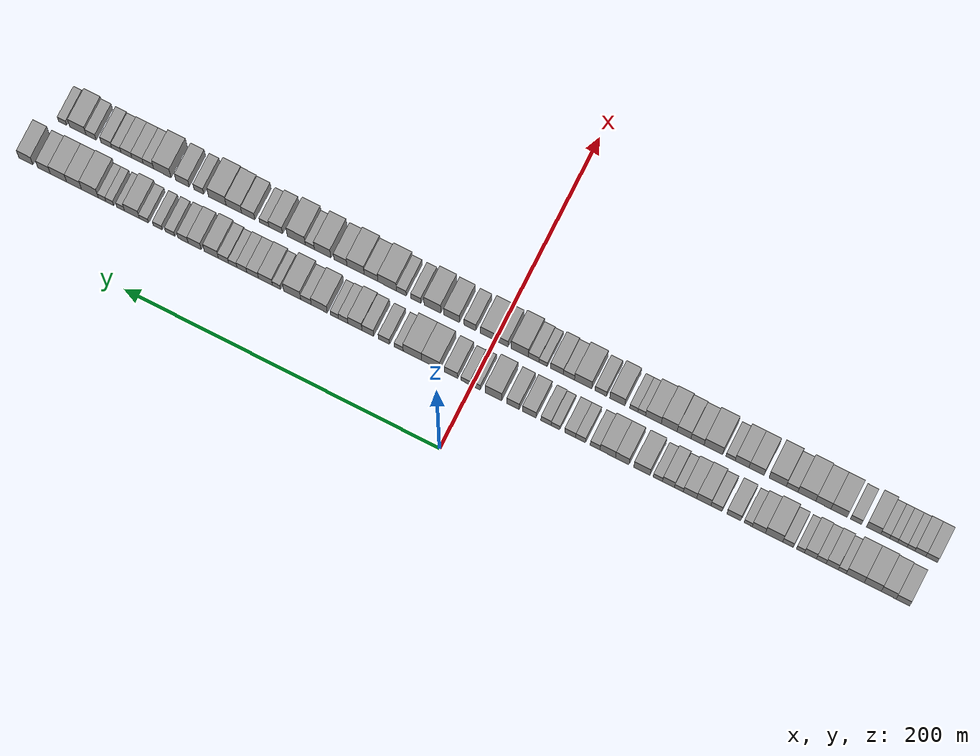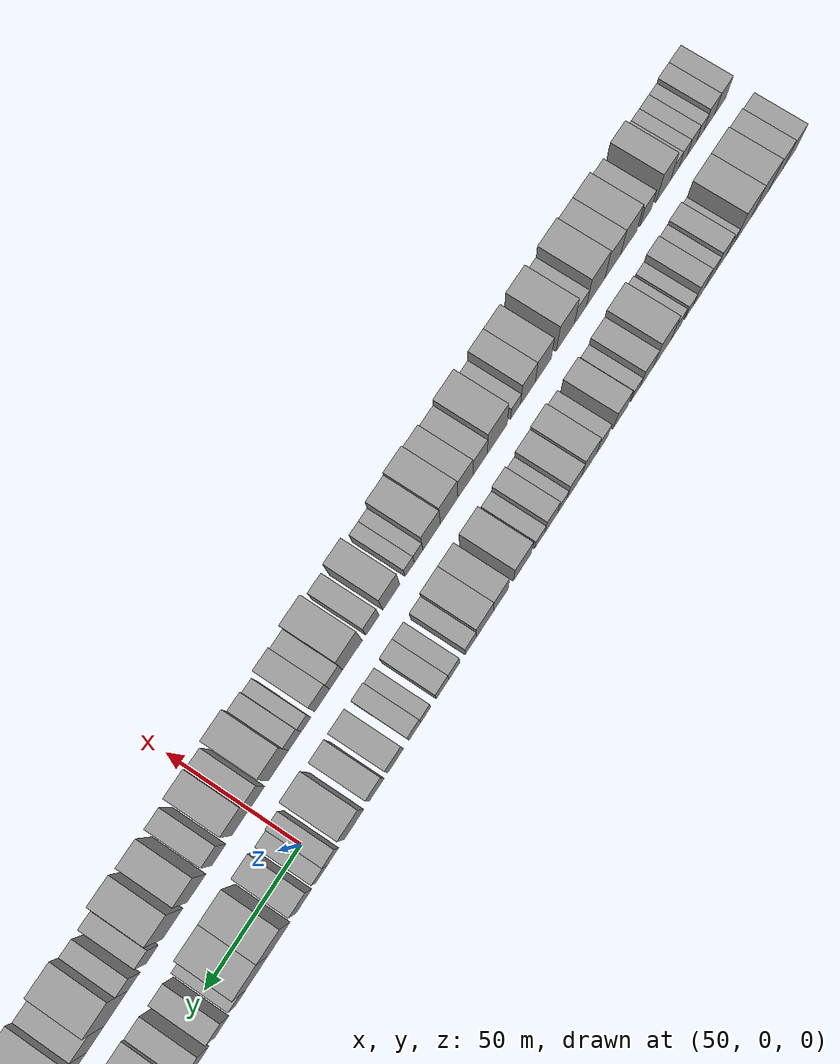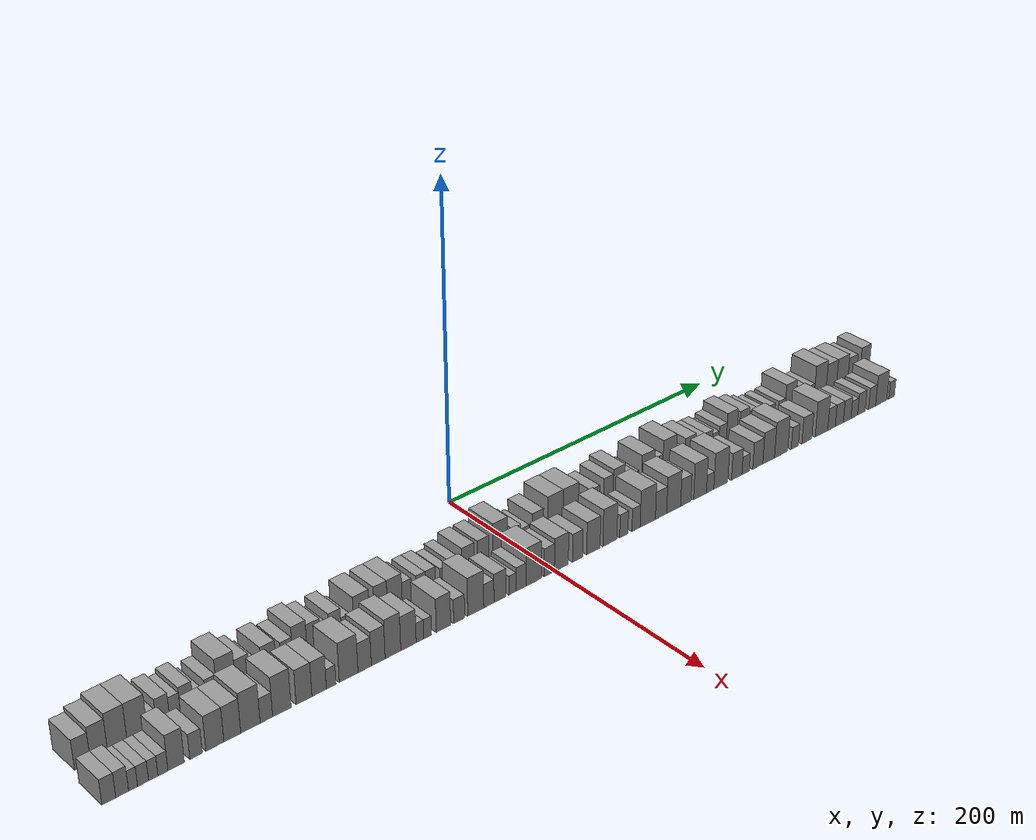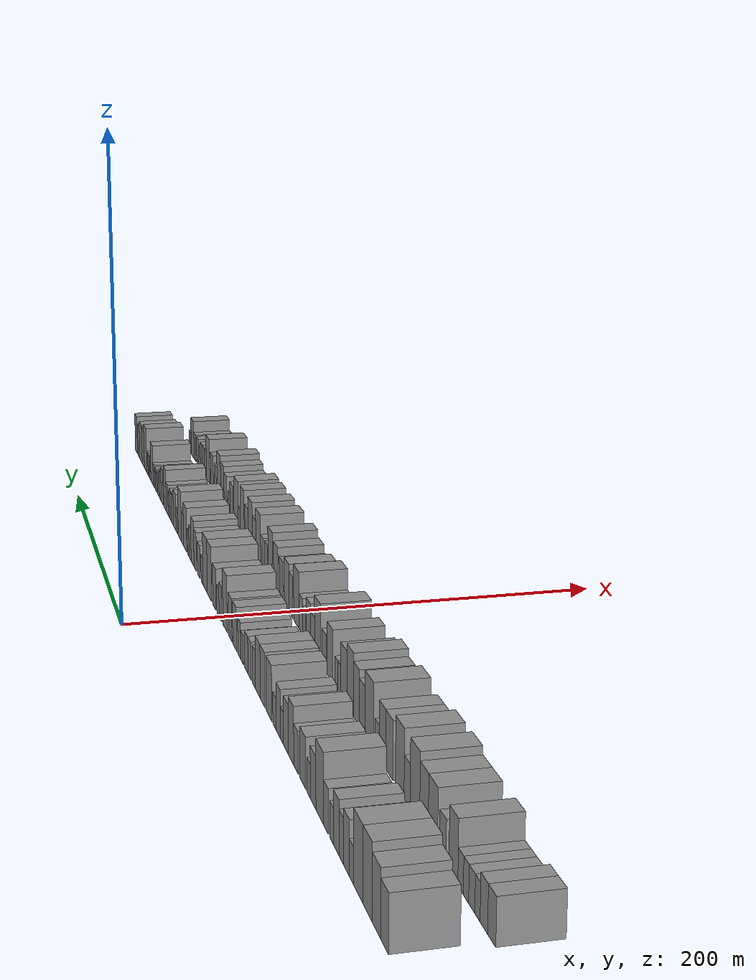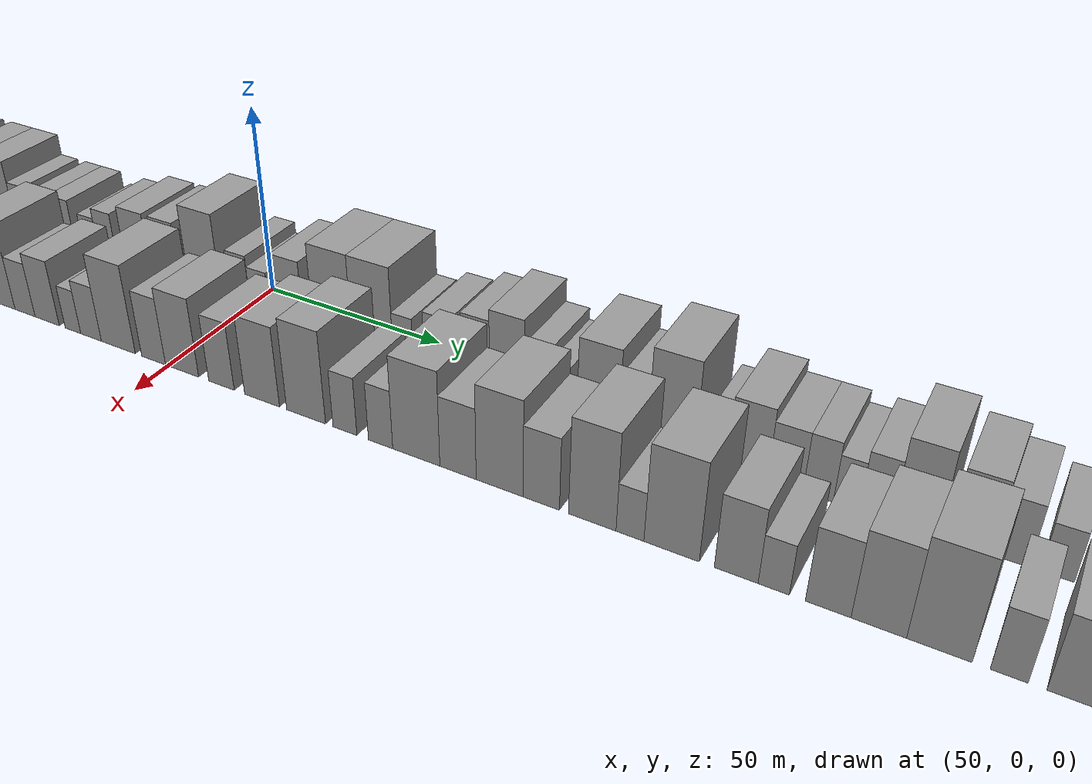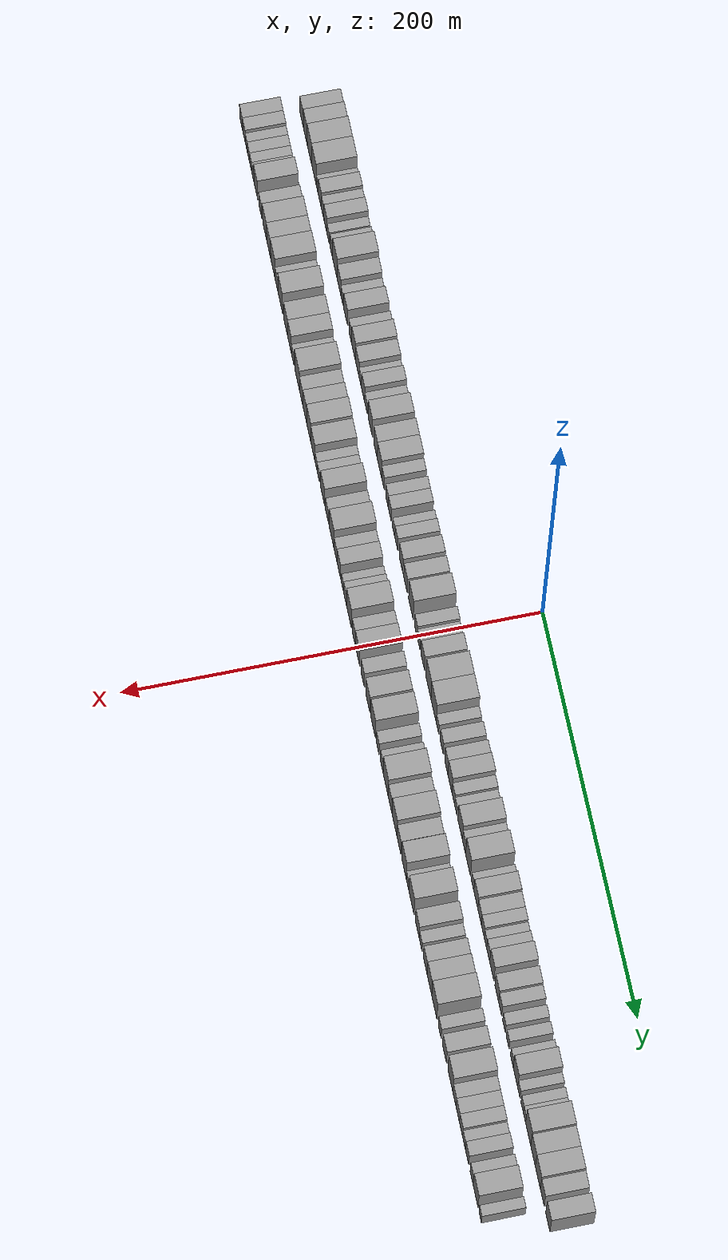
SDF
<sdf version="1.6">
 <world name="default">
  <scene>
   <sky><clouds><speed>12</speed></clouds></sky>
   <ambient>0.4 0.4 0.4 1</ambient>
   <background>0.7 0.7 0.7 1</background>
   <shadows>1</shadows>
  </scene>
  <gravity>0 0 -9.8066</gravity>
  <magnetic_field>6e-06 2.3e-05 -4.2e-05</magnetic_field>
  <physics default="0" name="default_physics" type="ode">
   <ode>
    <solver>
     <type>quick</type>
     <iters>10</iters>
     <sor>1.0</sor>
     <use_dynamic_moi_rescaling>0</use_dynamic_moi_rescaling>
    </solver>
    <constraints>
     <cfm>0</cfm>
     <erp>0.2</erp>
     <contact_max_correcting_vel>100</contact_max_correcting_vel>
     <contact_surface_layer>0.001</contact_surface_layer>
    </constraints>
   </ode>
   <max_step_size>0.004</max_step_size>
   <real_time_factor>1</real_time_factor>
   <real_time_update_rate>250</real_time_update_rate>
  </physics>
  <light name="sun" type="directional">
   <pose>0 0 10 0 0 0</pose>
   <diffuse>0.8 0.8 0.8 1</diffuse>
   <specular>0.2 0.2 0.2 1</specular>
   <attenuation>
    <range>1000</range>
    <constant>0.9</constant>
    <linear>0.01</linear>
    <quadratic>0.001</quadratic>
   </attenuation>
   <direction>-0.5 0.1 -0.9</direction>
  </light>
  <model name="building_1">
   <static>1</static>
   <pose>50.0000 -270.7462 0 0.000000 0.000000 0.000000</pose>
   <link name="link">
    <pose>0 0 9.00 0 0 0</pose>
    <collision name="collision"><geometry><box><size>20.0000 8.5076 18.0000</size></box></geometry></collision>
    <visual name="visual">
     <cast_shadows>0</cast_shadows>
     <geometry><box><size>20.0000 8.5076 18.0000</size></box></geometry>
     <material>
      <script>
       <uri>model://grey_wall/materials/scripts</uri>
       <uri>model://grey_wall/materials/textures</uri>
       <name>vrc/grey_wall</name>
      </script>
     </material>
    </visual>
   </link>
  </model>
  <model name="building_2">
   <static>1</static>
   <pose>50.0000 -261.8234 0 0.000000 0.000000 0.000000</pose>
   <link name="link">
    <pose>0 0 10.50 0 0 0</pose>
    <collision name="collision"><geometry><box><size>20.0000 9.3380 21.0000</size></box></geometry></collision>
    <visual name="visual">
     <cast_shadows>0</cast_shadows>
     <geometry><box><size>20.0000 9.3380 21.0000</size></box></geometry>
     <material>
      <script>
       <uri>model://grey_wall/materials/scripts</uri>
       <uri>model://grey_wall/materials/textures</uri>
       <name>vrc/grey_wall</name>
      </script>
     </material>
    </visual>
   </link>
  </model>
  <model name="building_3">
   <static>1</static>
   <pose>50.0000 -251.8180 0 0.000000 0.000000 0.000000</pose>
   <link name="link">
    <pose>0 0 12.00 0 0 0</pose>
    <collision name="collision"><geometry><box><size>20.0000 10.6729 24.0000</size></box></geometry></collision>
    <visual name="visual">
     <cast_shadows>0</cast_shadows>
     <geometry><box><size>20.0000 10.6729 24.0000</size></box></geometry>
     <material>
      <script>
       <uri>model://grey_wall/materials/scripts</uri>
       <uri>model://grey_wall/materials/textures</uri>
       <name>vrc/grey_wall</name>
      </script>
     </material>
    </visual>
   </link>
  </model>
  <model name="building_4">
   <static>1</static>
   <pose>50.0000 -240.9079 0 0.000000 0.000000 0.000000</pose>
   <link name="link">
    <pose>0 0 12.00 0 0 0</pose>
    <collision name="collision"><geometry><box><size>20.0000 11.1472 24.0000</size></box></geometry></collision>
    <visual name="visual">
     <cast_shadows>0</cast_shadows>
     <geometry><box><size>20.0000 11.1472 24.0000</size></box></geometry>
     <material>
      <script>
       <uri>model://grey_wall/materials/scripts</uri>
       <uri>model://grey_wall/materials/textures</uri>
       <name>vrc/grey_wall</name>
      </script>
     </material>
    </visual>
   </link>
  </model>
  <model name="building_5">
   <static>1</static>
   <pose>50.0000 -232.7691 0 0.000000 0.000000 0.000000</pose>
   <link name="link">
    <pose>0 0 6.00 0 0 0</pose>
    <collision name="collision"><geometry><box><size>20.0000 5.1303 12.0000</size></box></geometry></collision>
    <visual name="visual">
     <cast_shadows>0</cast_shadows>
     <geometry><box><size>20.0000 5.1303 12.0000</size></box></geometry>
     <material>
      <script>
       <uri>model://grey_wall/materials/scripts</uri>
       <uri>model://grey_wall/materials/textures</uri>
       <name>vrc/grey_wall</name>
      </script>
     </material>
    </visual>
   </link>
  </model>
  <model name="building_6">
   <static>1</static>
   <pose>50.0000 -226.4638 0 0.000000 0.000000 0.000000</pose>
   <link name="link">
    <pose>0 0 9.00 0 0 0</pose>
    <collision name="collision"><geometry><box><size>20.0000 7.4803 18.0000</size></box></geometry></collision>
    <visual name="visual">
     <cast_shadows>0</cast_shadows>
     <geometry><box><size>20.0000 7.4803 18.0000</size></box></geometry>
     <material>
      <script>
       <uri>model://grey_wall/materials/scripts</uri>
       <uri>model://grey_wall/materials/textures</uri>
       <name>vrc/grey_wall</name>
      </script>
     </material>
    </visual>
   </link>
  </model>
  <model name="building_7">
   <static>1</static>
   <pose>50.0000 -219.6944 0 0.000000 0.000000 0.000000</pose>
   <link name="link">
    <pose>0 0 7.50 0 0 0</pose>
    <collision name="collision"><geometry><box><size>20.0000 6.0585 15.0000</size></box></geometry></collision>
    <visual name="visual">
     <cast_shadows>0</cast_shadows>
     <geometry><box><size>20.0000 6.0585 15.0000</size></box></geometry>
     <material>
      <script>
       <uri>model://grey_wall/materials/scripts</uri>
       <uri>model://grey_wall/materials/textures</uri>
       <name>vrc/grey_wall</name>
      </script>
     </material>
    </visual>
   </link>
  </model>
  <model name="building_8">
   <static>1</static>
   <pose>50.0000 -212.9263 0 0.000000 0.000000 0.000000</pose>
   <link name="link">
    <pose>0 0 9.00 0 0 0</pose>
    <collision name="collision"><geometry><box><size>20.0000 7.4778 18.0000</size></box></geometry></collision>
    <visual name="visual">
     <cast_shadows>0</cast_shadows>
     <geometry><box><size>20.0000 7.4778 18.0000</size></box></geometry>
     <material>
      <script>
       <uri>model://grey_wall/materials/scripts</uri>
       <uri>model://grey_wall/materials/textures</uri>
       <name>vrc/grey_wall</name>
      </script>
     </material>
    </visual>
   </link>
  </model>
  <model name="building_9">
   <static>1</static>
   <pose>50.0000 -206.6918 0 0.000000 0.000000 0.000000</pose>
   <link name="link">
    <pose>0 0 6.00 0 0 0</pose>
    <collision name="collision"><geometry><box><size>20.0000 4.9912 12.0000</size></box></geometry></collision>
    <visual name="visual">
     <cast_shadows>0</cast_shadows>
     <geometry><box><size>20.0000 4.9912 12.0000</size></box></geometry>
     <material>
      <script>
       <uri>model://grey_wall/materials/scripts</uri>
       <uri>model://grey_wall/materials/textures</uri>
       <name>vrc/grey_wall</name>
      </script>
     </material>
    </visual>
   </link>
  </model>
  <model name="building_10">
   <static>1</static>
   <pose>50.0000 -198.9097 0 0.000000 0.000000 0.000000</pose>
   <link name="link">
    <pose>0 0 7.50 0 0 0</pose>
    <collision name="collision"><geometry><box><size>20.0000 6.5731 15.0000</size></box></geometry></collision>
    <visual name="visual">
     <cast_shadows>0</cast_shadows>
     <geometry><box><size>20.0000 6.5731 15.0000</size></box></geometry>
     <material>
      <script>
       <uri>model://grey_wall/materials/scripts</uri>
       <uri>model://grey_wall/materials/textures</uri>
       <name>vrc/grey_wall</name>
      </script>
     </material>
    </visual>
   </link>
  </model>
  <model name="building_11">
   <static>1</static>
   <pose>50.0000 -190.1880 0 0.000000 0.000000 0.000000</pose>
   <link name="link">
    <pose>0 0 12.00 0 0 0</pose>
    <collision name="collision"><geometry><box><size>20.0000 10.8702 24.0000</size></box></geometry></collision>
    <visual name="visual">
     <cast_shadows>0</cast_shadows>
     <geometry><box><size>20.0000 10.8702 24.0000</size></box></geometry>
     <material>
      <script>
       <uri>model://grey_wall/materials/scripts</uri>
       <uri>model://grey_wall/materials/textures</uri>
       <name>vrc/grey_wall</name>
      </script>
     </material>
    </visual>
   </link>
  </model>
  <model name="building_12">
   <static>1</static>
   <pose>50.0000 -180.5997 0 0.000000 0.000000 0.000000</pose>
   <link name="link">
    <pose>0 0 9.00 0 0 0</pose>
    <collision name="collision"><geometry><box><size>20.0000 8.3064 18.0000</size></box></geometry></collision>
    <visual name="visual">
     <cast_shadows>0</cast_shadows>
     <geometry><box><size>20.0000 8.3064 18.0000</size></box></geometry>
     <material>
      <script>
       <uri>model://grey_wall/materials/scripts</uri>
       <uri>model://grey_wall/materials/textures</uri>
       <name>vrc/grey_wall</name>
      </script>
     </material>
    </visual>
   </link>
  </model>
  <model name="building_13">
   <static>1</static>
   <pose>50.0000 -173.8752 0 0.000000 0.000000 0.000000</pose>
   <link name="link">
    <pose>0 0 6.00 0 0 0</pose>
    <collision name="collision"><geometry><box><size>20.0000 5.1427 12.0000</size></box></geometry></collision>
    <visual name="visual">
     <cast_shadows>0</cast_shadows>
     <geometry><box><size>20.0000 5.1427 12.0000</size></box></geometry>
     <material>
      <script>
       <uri>model://grey_wall/materials/scripts</uri>
       <uri>model://grey_wall/materials/textures</uri>
       <name>vrc/grey_wall</name>
      </script>
     </material>
    </visual>
   </link>
  </model>
  <model name="building_14">
   <static>1</static>
   <pose>50.0000 -164.9254 0 0.000000 0.000000 0.000000</pose>
   <link name="link">
    <pose>0 0 9.00 0 0 0</pose>
    <collision name="collision"><geometry><box><size>20.0000 8.7569 18.0000</size></box></geometry></collision>
    <visual name="visual">
     <cast_shadows>0</cast_shadows>
     <geometry><box><size>20.0000 8.7569 18.0000</size></box></geometry>
     <material>
      <script>
       <uri>model://grey_wall/materials/scripts</uri>
       <uri>model://grey_wall/materials/textures</uri>
       <name>vrc/grey_wall</name>
      </script>
     </material>
    </visual>
   </link>
  </model>
  <model name="building_15">
   <static>1</static>
   <pose>50.0000 -154.0397 0 0.000000 0.000000 0.000000</pose>
   <link name="link">
    <pose>0 0 7.50 0 0 0</pose>
    <collision name="collision"><geometry><box><size>20.0000 7.0144 15.0000</size></box></geometry></collision>
    <visual name="visual">
     <cast_shadows>0</cast_shadows>
     <geometry><box><size>20.0000 7.0144 15.0000</size></box></geometry>
     <material>
      <script>
       <uri>model://grey_wall/materials/scripts</uri>
       <uri>model://grey_wall/materials/textures</uri>
       <name>vrc/grey_wall</name>
      </script>
     </material>
    </visual>
   </link>
  </model>
  <model name="building_16">
   <static>1</static>
   <pose>50.0000 -146.1024 0 0.000000 0.000000 0.000000</pose>
   <link name="link">
    <pose>0 0 10.50 0 0 0</pose>
    <collision name="collision"><geometry><box><size>20.0000 8.8601 21.0000</size></box></geometry></collision>
    <visual name="visual">
     <cast_shadows>0</cast_shadows>
     <geometry><box><size>20.0000 8.8601 21.0000</size></box></geometry>
     <material>
      <script>
       <uri>model://grey_wall/materials/scripts</uri>
       <uri>model://grey_wall/materials/textures</uri>
       <name>vrc/grey_wall</name>
      </script>
     </material>
    </visual>
   </link>
  </model>
  <model name="building_17">
   <static>1</static>
   <pose>50.0000 -137.4521 0 0.000000 0.000000 0.000000</pose>
   <link name="link">
    <pose>0 0 9.00 0 0 0</pose>
    <collision name="collision"><geometry><box><size>20.0000 8.4406 18.0000</size></box></geometry></collision>
    <visual name="visual">
     <cast_shadows>0</cast_shadows>
     <geometry><box><size>20.0000 8.4406 18.0000</size></box></geometry>
     <material>
      <script>
       <uri>model://grey_wall/materials/scripts</uri>
       <uri>model://grey_wall/materials/textures</uri>
       <name>vrc/grey_wall</name>
      </script>
     </material>
    </visual>
   </link>
  </model>
  <model name="building_18">
   <static>1</static>
   <pose>50.0000 -130.4645 0 0.000000 0.000000 0.000000</pose>
   <link name="link">
    <pose>0 0 6.00 0 0 0</pose>
    <collision name="collision"><geometry><box><size>20.0000 5.5346 12.0000</size></box></geometry></collision>
    <visual name="visual">
     <cast_shadows>0</cast_shadows>
     <geometry><box><size>20.0000 5.5346 12.0000</size></box></geometry>
     <material>
      <script>
       <uri>model://grey_wall/materials/scripts</uri>
       <uri>model://grey_wall/materials/textures</uri>
       <name>vrc/grey_wall</name>
      </script>
     </material>
    </visual>
   </link>
  </model>
  <model name="building_19">
   <static>1</static>
   <pose>50.0000 -123.9493 0 0.000000 0.000000 0.000000</pose>
   <link name="link">
    <pose>0 0 9.00 0 0 0</pose>
    <collision name="collision"><geometry><box><size>20.0000 7.4958 18.0000</size></box></geometry></collision>
    <visual name="visual">
     <cast_shadows>0</cast_shadows>
     <geometry><box><size>20.0000 7.4958 18.0000</size></box></geometry>
     <material>
      <script>
       <uri>model://grey_wall/materials/scripts</uri>
       <uri>model://grey_wall/materials/textures</uri>
       <name>vrc/grey_wall</name>
      </script>
     </material>
    </visual>
   </link>
  </model>
  <model name="building_20">
   <static>1</static>
   <pose>50.0000 -117.2490 0 0.000000 0.000000 0.000000</pose>
   <link name="link">
    <pose>0 0 6.00 0 0 0</pose>
    <collision name="collision"><geometry><box><size>20.0000 5.9047 12.0000</size></box></geometry></collision>
    <visual name="visual">
     <cast_shadows>0</cast_shadows>
     <geometry><box><size>20.0000 5.9047 12.0000</size></box></geometry>
     <material>
      <script>
       <uri>model://grey_wall/materials/scripts</uri>
       <uri>model://grey_wall/materials/textures</uri>
       <name>vrc/grey_wall</name>
      </script>
     </material>
    </visual>
   </link>
  </model>
  <model name="building_21">
   <static>1</static>
   <pose>50.0000 -107.1935 0 0.000000 0.000000 0.000000</pose>
   <link name="link">
    <pose>0 0 10.50 0 0 0</pose>
    <collision name="collision"><geometry><box><size>20.0000 10.2065 21.0000</size></box></geometry></collision>
    <visual name="visual">
     <cast_shadows>0</cast_shadows>
     <geometry><box><size>20.0000 10.2065 21.0000</size></box></geometry>
     <material>
      <script>
       <uri>model://grey_wall/materials/scripts</uri>
       <uri>model://grey_wall/materials/textures</uri>
       <name>vrc/grey_wall</name>
      </script>
     </material>
    </visual>
   </link>
  </model>
  <model name="building_22">
   <static>1</static>
   <pose>50.0000 -94.8351 0 0.000000 0.000000 0.000000</pose>
   <link name="link">
    <pose>0 0 10.50 0 0 0</pose>
    <collision name="collision"><geometry><box><size>20.0000 8.5103 21.0000</size></box></geometry></collision>
    <visual name="visual">
     <cast_shadows>0</cast_shadows>
     <geometry><box><size>20.0000 8.5103 21.0000</size></box></geometry>
     <material>
      <script>
       <uri>model://grey_wall/materials/scripts</uri>
       <uri>model://grey_wall/materials/textures</uri>
       <name>vrc/grey_wall</name>
      </script>
     </material>
    </visual>
   </link>
  </model>
  <model name="building_23">
   <static>1</static>
   <pose>50.0000 -85.7295 0 0.000000 0.000000 0.000000</pose>
   <link name="link">
    <pose>0 0 10.50 0 0 0</pose>
    <collision name="collision"><geometry><box><size>20.0000 9.7010 21.0000</size></box></geometry></collision>
    <visual name="visual">
     <cast_shadows>0</cast_shadows>
     <geometry><box><size>20.0000 9.7010 21.0000</size></box></geometry>
     <material>
      <script>
       <uri>model://grey_wall/materials/scripts</uri>
       <uri>model://grey_wall/materials/textures</uri>
       <name>vrc/grey_wall</name>
      </script>
     </material>
    </visual>
   </link>
  </model>
  <model name="building_24">
   <static>1</static>
   <pose>50.0000 -77.7669 0 0.000000 0.000000 0.000000</pose>
   <link name="link">
    <pose>0 0 7.50 0 0 0</pose>
    <collision name="collision"><geometry><box><size>20.0000 6.2241 15.0000</size></box></geometry></collision>
    <visual name="visual">
     <cast_shadows>0</cast_shadows>
     <geometry><box><size>20.0000 6.2241 15.0000</size></box></geometry>
     <material>
      <script>
       <uri>model://grey_wall/materials/scripts</uri>
       <uri>model://grey_wall/materials/textures</uri>
       <name>vrc/grey_wall</name>
      </script>
     </material>
    </visual>
   </link>
  </model>
  <model name="building_25">
   <static>1</static>
   <pose>50.0000 -68.5766 0 0.000000 0.000000 0.000000</pose>
   <link name="link">
    <pose>0 0 7.50 0 0 0</pose>
    <collision name="collision"><geometry><box><size>20.0000 6.1565 15.0000</size></box></geometry></collision>
    <visual name="visual">
     <cast_shadows>0</cast_shadows>
     <geometry><box><size>20.0000 6.1565 15.0000</size></box></geometry>
     <material>
      <script>
       <uri>model://grey_wall/materials/scripts</uri>
       <uri>model://grey_wall/materials/textures</uri>
       <name>vrc/grey_wall</name>
      </script>
     </material>
    </visual>
   </link>
  </model>
  <model name="building_26">
   <static>1</static>
   <pose>50.0000 -62.0209 0 0.000000 0.000000 0.000000</pose>
   <link name="link">
    <pose>0 0 7.50 0 0 0</pose>
    <collision name="collision"><geometry><box><size>20.0000 6.9550 15.0000</size></box></geometry></collision>
    <visual name="visual">
     <cast_shadows>0</cast_shadows>
     <geometry><box><size>20.0000 6.9550 15.0000</size></box></geometry>
     <material>
      <script>
       <uri>model://grey_wall/materials/scripts</uri>
       <uri>model://grey_wall/materials/textures</uri>
       <name>vrc/grey_wall</name>
      </script>
     </material>
    </visual>
   </link>
  </model>
  <model name="building_27">
   <static>1</static>
   <pose>50.0000 -52.7724 0 0.000000 0.000000 0.000000</pose>
   <link name="link">
    <pose>0 0 6.00 0 0 0</pose>
    <collision name="collision"><geometry><box><size>20.0000 5.5420 12.0000</size></box></geometry></collision>
    <visual name="visual">
     <cast_shadows>0</cast_shadows>
     <geometry><box><size>20.0000 5.5420 12.0000</size></box></geometry>
     <material>
      <script>
       <uri>model://grey_wall/materials/scripts</uri>
       <uri>model://grey_wall/materials/textures</uri>
       <name>vrc/grey_wall</name>
      </script>
     </material>
    </visual>
   </link>
  </model>
  <model name="building_28">
   <static>1</static>
   <pose>50.0000 -46.7659 0 0.000000 0.000000 0.000000</pose>
   <link name="link">
    <pose>0 0 7.50 0 0 0</pose>
    <collision name="collision"><geometry><box><size>20.0000 6.4709 15.0000</size></box></geometry></collision>
    <visual name="visual">
     <cast_shadows>0</cast_shadows>
     <geometry><box><size>20.0000 6.4709 15.0000</size></box></geometry>
     <material>
      <script>
       <uri>model://grey_wall/materials/scripts</uri>
       <uri>model://grey_wall/materials/textures</uri>
       <name>vrc/grey_wall</name>
      </script>
     </material>
    </visual>
   </link>
  </model>
  <model name="building_29">
   <static>1</static>
   <pose>50.0000 -36.2263 0 0.000000 0.000000 0.000000</pose>
   <link name="link">
    <pose>0 0 9.00 0 0 0</pose>
    <collision name="collision"><geometry><box><size>20.0000 8.6084 18.0000</size></box></geometry></collision>
    <visual name="visual">
     <cast_shadows>0</cast_shadows>
     <geometry><box><size>20.0000 8.6084 18.0000</size></box></geometry>
     <material>
      <script>
       <uri>model://grey_wall/materials/scripts</uri>
       <uri>model://grey_wall/materials/textures</uri>
       <name>vrc/grey_wall</name>
      </script>
     </material>
    </visual>
   </link>
  </model>
  <model name="building_30">
   <static>1</static>
   <pose>50.0000 -25.9120 0 0.000000 0.000000 0.000000</pose>
   <link name="link">
    <pose>0 0 9.00 0 0 0</pose>
    <collision name="collision"><geometry><box><size>20.0000 8.0202 18.0000</size></box></geometry></collision>
    <visual name="visual">
     <cast_shadows>0</cast_shadows>
     <geometry><box><size>20.0000 8.0202 18.0000</size></box></geometry>
     <material>
      <script>
       <uri>model://grey_wall/materials/scripts</uri>
       <uri>model://grey_wall/materials/textures</uri>
       <name>vrc/grey_wall</name>
      </script>
     </material>
    </visual>
   </link>
  </model>
  <model name="building_31">
   <static>1</static>
   <pose>50.0000 -13.6503 0 0.000000 0.000000 0.000000</pose>
   <link name="link">
    <pose>0 0 12.00 0 0 0</pose>
    <collision name="collision"><geometry><box><size>20.0000 10.5032 24.0000</size></box></geometry></collision>
    <visual name="visual">
     <cast_shadows>0</cast_shadows>
     <geometry><box><size>20.0000 10.5032 24.0000</size></box></geometry>
     <material>
      <script>
       <uri>model://grey_wall/materials/scripts</uri>
       <uri>model://grey_wall/materials/textures</uri>
       <name>vrc/grey_wall</name>
      </script>
     </material>
    </visual>
   </link>
  </model>
  <model name="building_32">
   <static>1</static>
   <pose>50.0000 -2.2336 0 0.000000 0.000000 0.000000</pose>
   <link name="link">
    <pose>0 0 7.50 0 0 0</pose>
    <collision name="collision"><geometry><box><size>20.0000 6.3303 15.0000</size></box></geometry></collision>
    <visual name="visual">
     <cast_shadows>0</cast_shadows>
     <geometry><box><size>20.0000 6.3303 15.0000</size></box></geometry>
     <material>
      <script>
       <uri>model://grey_wall/materials/scripts</uri>
       <uri>model://grey_wall/materials/textures</uri>
       <name>vrc/grey_wall</name>
      </script>
     </material>
    </visual>
   </link>
  </model>
  <model name="building_33">
   <static>1</static>
   <pose>50.0000 3.9265 0 0.000000 0.000000 0.000000</pose>
   <link name="link">
    <pose>0 0 6.00 0 0 0</pose>
    <collision name="collision"><geometry><box><size>20.0000 5.9898 12.0000</size></box></geometry></collision>
    <visual name="visual">
     <cast_shadows>0</cast_shadows>
     <geometry><box><size>20.0000 5.9898 12.0000</size></box></geometry>
     <material>
      <script>
       <uri>model://grey_wall/materials/scripts</uri>
       <uri>model://grey_wall/materials/textures</uri>
       <name>vrc/grey_wall</name>
      </script>
     </material>
    </visual>
   </link>
  </model>
  <model name="building_34">
   <static>1</static>
   <pose>50.0000 13.1047 0 0.000000 0.000000 0.000000</pose>
   <link name="link">
    <pose>0 0 9.00 0 0 0</pose>
    <collision name="collision"><geometry><box><size>20.0000 8.3667 18.0000</size></box></geometry></collision>
    <visual name="visual">
     <cast_shadows>0</cast_shadows>
     <geometry><box><size>20.0000 8.3667 18.0000</size></box></geometry>
     <material>
      <script>
       <uri>model://grey_wall/materials/scripts</uri>
       <uri>model://grey_wall/materials/textures</uri>
       <name>vrc/grey_wall</name>
      </script>
     </material>
    </visual>
   </link>
  </model>
  <model name="building_35">
   <static>1</static>
   <pose>50.0000 25.9832 0 0.000000 0.000000 0.000000</pose>
   <link name="link">
    <pose>0 0 12.00 0 0 0</pose>
    <collision name="collision"><geometry><box><size>20.0000 11.3902 24.0000</size></box></geometry></collision>
    <visual name="visual">
     <cast_shadows>0</cast_shadows>
     <geometry><box><size>20.0000 11.3902 24.0000</size></box></geometry>
     <material>
      <script>
       <uri>model://grey_wall/materials/scripts</uri>
       <uri>model://grey_wall/materials/textures</uri>
       <name>vrc/grey_wall</name>
      </script>
     </material>
    </visual>
   </link>
  </model>
  <model name="building_36">
   <static>1</static>
   <pose>50.0000 37.5372 0 0.000000 0.000000 0.000000</pose>
   <link name="link">
    <pose>0 0 12.00 0 0 0</pose>
    <collision name="collision"><geometry><box><size>20.0000 11.7177 24.0000</size></box></geometry></collision>
    <visual name="visual">
     <cast_shadows>0</cast_shadows>
     <geometry><box><size>20.0000 11.7177 24.0000</size></box></geometry>
     <material>
      <script>
       <uri>model://grey_wall/materials/scripts</uri>
       <uri>model://grey_wall/materials/textures</uri>
       <name>vrc/grey_wall</name>
      </script>
     </material>
    </visual>
   </link>
  </model>
  <model name="building_37">
   <static>1</static>
   <pose>50.0000 46.2099 0 0.000000 0.000000 0.000000</pose>
   <link name="link">
    <pose>0 0 6.00 0 0 0</pose>
    <collision name="collision"><geometry><box><size>20.0000 5.6278 12.0000</size></box></geometry></collision>
    <visual name="visual">
     <cast_shadows>0</cast_shadows>
     <geometry><box><size>20.0000 5.6278 12.0000</size></box></geometry>
     <material>
      <script>
       <uri>model://grey_wall/materials/scripts</uri>
       <uri>model://grey_wall/materials/textures</uri>
       <name>vrc/grey_wall</name>
      </script>
     </material>
    </visual>
   </link>
  </model>
  <model name="building_38">
   <static>1</static>
   <pose>50.0000 55.5786 0 0.000000 0.000000 0.000000</pose>
   <link name="link">
    <pose>0 0 7.50 0 0 0</pose>
    <collision name="collision"><geometry><box><size>20.0000 7.1096 15.0000</size></box></geometry></collision>
    <visual name="visual">
     <cast_shadows>0</cast_shadows>
     <geometry><box><size>20.0000 7.1096 15.0000</size></box></geometry>
     <material>
      <script>
       <uri>model://grey_wall/materials/scripts</uri>
       <uri>model://grey_wall/materials/textures</uri>
       <name>vrc/grey_wall</name>
      </script>
     </material>
    </visual>
   </link>
  </model>
  <model name="building_39">
   <static>1</static>
   <pose>50.0000 65.8306 0 0.000000 0.000000 0.000000</pose>
   <link name="link">
    <pose>0 0 9.00 0 0 0</pose>
    <collision name="collision"><geometry><box><size>20.0000 7.3943 18.0000</size></box></geometry></collision>
    <visual name="visual">
     <cast_shadows>0</cast_shadows>
     <geometry><box><size>20.0000 7.3943 18.0000</size></box></geometry>
     <material>
      <script>
       <uri>model://grey_wall/materials/scripts</uri>
       <uri>model://grey_wall/materials/textures</uri>
       <name>vrc/grey_wall</name>
      </script>
     </material>
    </visual>
   </link>
  </model>
  <model name="building_40">
   <static>1</static>
   <pose>50.0000 73.9746 0 0.000000 0.000000 0.000000</pose>
   <link name="link">
    <pose>0 0 10.50 0 0 0</pose>
    <collision name="collision"><geometry><box><size>20.0000 8.8938 21.0000</size></box></geometry></collision>
    <visual name="visual">
     <cast_shadows>0</cast_shadows>
     <geometry><box><size>20.0000 8.8938 21.0000</size></box></geometry>
     <material>
      <script>
       <uri>model://grey_wall/materials/scripts</uri>
       <uri>model://grey_wall/materials/textures</uri>
       <name>vrc/grey_wall</name>
      </script>
     </material>
    </visual>
   </link>
  </model>
  <model name="building_41">
   <static>1</static>
   <pose>50.0000 81.4546 0 0.000000 0.000000 0.000000</pose>
   <link name="link">
    <pose>0 0 7.50 0 0 0</pose>
    <collision name="collision"><geometry><box><size>20.0000 6.0662 15.0000</size></box></geometry></collision>
    <visual name="visual">
     <cast_shadows>0</cast_shadows>
     <geometry><box><size>20.0000 6.0662 15.0000</size></box></geometry>
     <material>
      <script>
       <uri>model://grey_wall/materials/scripts</uri>
       <uri>model://grey_wall/materials/textures</uri>
       <name>vrc/grey_wall</name>
      </script>
     </material>
    </visual>
   </link>
  </model>
  <model name="building_42">
   <static>1</static>
   <pose>50.0000 87.0253 0 0.000000 0.000000 0.000000</pose>
   <link name="link">
    <pose>0 0 6.00 0 0 0</pose>
    <collision name="collision"><geometry><box><size>20.0000 5.0752 12.0000</size></box></geometry></collision>
    <visual name="visual">
     <cast_shadows>0</cast_shadows>
     <geometry><box><size>20.0000 5.0752 12.0000</size></box></geometry>
     <material>
      <script>
       <uri>model://grey_wall/materials/scripts</uri>
       <uri>model://grey_wall/materials/textures</uri>
       <name>vrc/grey_wall</name>
      </script>
     </material>
    </visual>
   </link>
  </model>
  <model name="building_43">
   <static>1</static>
   <pose>50.0000 96.6323 0 0.000000 0.000000 0.000000</pose>
   <link name="link">
    <pose>0 0 10.50 0 0 0</pose>
    <collision name="collision"><geometry><box><size>20.0000 10.1386 21.0000</size></box></geometry></collision>
    <visual name="visual">
     <cast_shadows>0</cast_shadows>
     <geometry><box><size>20.0000 10.1386 21.0000</size></box></geometry>
     <material>
      <script>
       <uri>model://grey_wall/materials/scripts</uri>
       <uri>model://grey_wall/materials/textures</uri>
       <name>vrc/grey_wall</name>
      </script>
     </material>
    </visual>
   </link>
  </model>
  <model name="building_44">
   <static>1</static>
   <pose>50.0000 105.0528 0 0.000000 0.000000 0.000000</pose>
   <link name="link">
    <pose>0 0 7.50 0 0 0</pose>
    <collision name="collision"><geometry><box><size>20.0000 6.7025 15.0000</size></box></geometry></collision>
    <visual name="visual">
     <cast_shadows>0</cast_shadows>
     <geometry><box><size>20.0000 6.7025 15.0000</size></box></geometry>
     <material>
      <script>
       <uri>model://grey_wall/materials/scripts</uri>
       <uri>model://grey_wall/materials/textures</uri>
       <name>vrc/grey_wall</name>
      </script>
     </material>
    </visual>
   </link>
  </model>
  <model name="building_45">
   <static>1</static>
   <pose>50.0000 113.8188 0 0.000000 0.000000 0.000000</pose>
   <link name="link">
    <pose>0 0 12.00 0 0 0</pose>
    <collision name="collision"><geometry><box><size>20.0000 10.8294 24.0000</size></box></geometry></collision>
    <visual name="visual">
     <cast_shadows>0</cast_shadows>
     <geometry><box><size>20.0000 10.8294 24.0000</size></box></geometry>
     <material>
      <script>
       <uri>model://grey_wall/materials/scripts</uri>
       <uri>model://grey_wall/materials/textures</uri>
       <name>vrc/grey_wall</name>
      </script>
     </material>
    </visual>
   </link>
  </model>
  <model name="building_46">
   <static>1</static>
   <pose>50.0000 123.8495 0 0.000000 0.000000 0.000000</pose>
   <link name="link">
    <pose>0 0 6.00 0 0 0</pose>
    <collision name="collision"><geometry><box><size>20.0000 5.2320 12.0000</size></box></geometry></collision>
    <visual name="visual">
     <cast_shadows>0</cast_shadows>
     <geometry><box><size>20.0000 5.2320 12.0000</size></box></geometry>
     <material>
      <script>
       <uri>model://grey_wall/materials/scripts</uri>
       <uri>model://grey_wall/materials/textures</uri>
       <name>vrc/grey_wall</name>
      </script>
     </material>
    </visual>
   </link>
  </model>
  <model name="building_47">
   <static>1</static>
   <pose>50.0000 130.8574 0 0.000000 0.000000 0.000000</pose>
   <link name="link">
    <pose>0 0 9.00 0 0 0</pose>
    <collision name="collision"><geometry><box><size>20.0000 8.7837 18.0000</size></box></geometry></collision>
    <visual name="visual">
     <cast_shadows>0</cast_shadows>
     <geometry><box><size>20.0000 8.7837 18.0000</size></box></geometry>
     <material>
      <script>
       <uri>model://grey_wall/materials/scripts</uri>
       <uri>model://grey_wall/materials/textures</uri>
       <name>vrc/grey_wall</name>
      </script>
     </material>
    </visual>
   </link>
  </model>
  <model name="building_48">
   <static>1</static>
   <pose>50.0000 138.9874 0 0.000000 0.000000 0.000000</pose>
   <link name="link">
    <pose>0 0 7.50 0 0 0</pose>
    <collision name="collision"><geometry><box><size>20.0000 7.4764 15.0000</size></box></geometry></collision>
    <visual name="visual">
     <cast_shadows>0</cast_shadows>
     <geometry><box><size>20.0000 7.4764 15.0000</size></box></geometry>
     <material>
      <script>
       <uri>model://grey_wall/materials/scripts</uri>
       <uri>model://grey_wall/materials/textures</uri>
       <name>vrc/grey_wall</name>
      </script>
     </material>
    </visual>
   </link>
  </model>
  <model name="building_49">
   <static>1</static>
   <pose>50.0000 145.8648 0 0.000000 0.000000 0.000000</pose>
   <link name="link">
    <pose>0 0 7.50 0 0 0</pose>
    <collision name="collision"><geometry><box><size>20.0000 6.2784 15.0000</size></box></geometry></collision>
    <visual name="visual">
     <cast_shadows>0</cast_shadows>
     <geometry><box><size>20.0000 6.2784 15.0000</size></box></geometry>
     <material>
      <script>
       <uri>model://grey_wall/materials/scripts</uri>
       <uri>model://grey_wall/materials/textures</uri>
       <name>vrc/grey_wall</name>
      </script>
     </material>
    </visual>
   </link>
  </model>
  <model name="building_50">
   <static>1</static>
   <pose>50.0000 151.6517 0 0.000000 0.000000 0.000000</pose>
   <link name="link">
    <pose>0 0 6.00 0 0 0</pose>
    <collision name="collision"><geometry><box><size>20.0000 5.2955 12.0000</size></box></geometry></collision>
    <visual name="visual">
     <cast_shadows>0</cast_shadows>
     <geometry><box><size>20.0000 5.2955 12.0000</size></box></geometry>
     <material>
      <script>
       <uri>model://grey_wall/materials/scripts</uri>
       <uri>model://grey_wall/materials/textures</uri>
       <name>vrc/grey_wall</name>
      </script>
     </material>
    </visual>
   </link>
  </model>
  <model name="building_51">
   <static>1</static>
   <pose>50.0000 157.5836 0 0.000000 0.000000 0.000000</pose>
   <link name="link">
    <pose>0 0 7.50 0 0 0</pose>
    <collision name="collision"><geometry><box><size>20.0000 6.5682 15.0000</size></box></geometry></collision>
    <visual name="visual">
     <cast_shadows>0</cast_shadows>
     <geometry><box><size>20.0000 6.5682 15.0000</size></box></geometry>
     <material>
      <script>
       <uri>model://grey_wall/materials/scripts</uri>
       <uri>model://grey_wall/materials/textures</uri>
       <name>vrc/grey_wall</name>
      </script>
     </material>
    </visual>
   </link>
  </model>
  <model name="building_52">
   <static>1</static>
   <pose>50.0000 165.3374 0 0.000000 0.000000 0.000000</pose>
   <link name="link">
    <pose>0 0 10.50 0 0 0</pose>
    <collision name="collision"><geometry><box><size>20.0000 8.9393 21.0000</size></box></geometry></collision>
    <visual name="visual">
     <cast_shadows>0</cast_shadows>
     <geometry><box><size>20.0000 8.9393 21.0000</size></box></geometry>
     <material>
      <script>
       <uri>model://grey_wall/materials/scripts</uri>
       <uri>model://grey_wall/materials/textures</uri>
       <name>vrc/grey_wall</name>
      </script>
     </material>
    </visual>
   </link>
  </model>
  <model name="building_53">
   <static>1</static>
   <pose>50.0000 175.9258 0 0.000000 0.000000 0.000000</pose>
   <link name="link">
    <pose>0 0 9.00 0 0 0</pose>
    <collision name="collision"><geometry><box><size>20.0000 8.2376 18.0000</size></box></geometry></collision>
    <visual name="visual">
     <cast_shadows>0</cast_shadows>
     <geometry><box><size>20.0000 8.2376 18.0000</size></box></geometry>
     <material>
      <script>
       <uri>model://grey_wall/materials/scripts</uri>
       <uri>model://grey_wall/materials/textures</uri>
       <name>vrc/grey_wall</name>
      </script>
     </material>
    </visual>
   </link>
  </model>
  <model name="building_54">
   <static>1</static>
   <pose>50.0000 183.3420 0 0.000000 0.000000 0.000000</pose>
   <link name="link">
    <pose>0 0 7.50 0 0 0</pose>
    <collision name="collision"><geometry><box><size>20.0000 6.5947 15.0000</size></box></geometry></collision>
    <visual name="visual">
     <cast_shadows>0</cast_shadows>
     <geometry><box><size>20.0000 6.5947 15.0000</size></box></geometry>
     <material>
      <script>
       <uri>model://grey_wall/materials/scripts</uri>
       <uri>model://grey_wall/materials/textures</uri>
       <name>vrc/grey_wall</name>
      </script>
     </material>
    </visual>
   </link>
  </model>
  <model name="building_55">
   <static>1</static>
   <pose>50.0000 191.6274 0 0.000000 0.000000 0.000000</pose>
   <link name="link">
    <pose>0 0 6.00 0 0 0</pose>
    <collision name="collision"><geometry><box><size>20.0000 5.9762 12.0000</size></box></geometry></collision>
    <visual name="visual">
     <cast_shadows>0</cast_shadows>
     <geometry><box><size>20.0000 5.9762 12.0000</size></box></geometry>
     <material>
      <script>
       <uri>model://grey_wall/materials/scripts</uri>
       <uri>model://grey_wall/materials/textures</uri>
       <name>vrc/grey_wall</name>
      </script>
     </material>
    </visual>
   </link>
  </model>
  <model name="building_56">
   <static>1</static>
   <pose>50.0000 199.4643 0 0.000000 0.000000 0.000000</pose>
   <link name="link">
    <pose>0 0 6.00 0 0 0</pose>
    <collision name="collision"><geometry><box><size>20.0000 5.6976 12.0000</size></box></geometry></collision>
    <visual name="visual">
     <cast_shadows>0</cast_shadows>
     <geometry><box><size>20.0000 5.6976 12.0000</size></box></geometry>
     <material>
      <script>
       <uri>model://grey_wall/materials/scripts</uri>
       <uri>model://grey_wall/materials/textures</uri>
       <name>vrc/grey_wall</name>
      </script>
     </material>
    </visual>
   </link>
  </model>
  <model name="building_57">
   <static>1</static>
   <pose>50.0000 208.2689 0 0.000000 0.000000 0.000000</pose>
   <link name="link">
    <pose>0 0 6.00 0 0 0</pose>
    <collision name="collision"><geometry><box><size>20.0000 5.9114 12.0000</size></box></geometry></collision>
    <visual name="visual">
     <cast_shadows>0</cast_shadows>
     <geometry><box><size>20.0000 5.9114 12.0000</size></box></geometry>
     <material>
      <script>
       <uri>model://grey_wall/materials/scripts</uri>
       <uri>model://grey_wall/materials/textures</uri>
       <name>vrc/grey_wall</name>
      </script>
     </material>
    </visual>
   </link>
  </model>
  <model name="building_58">
   <static>1</static>
   <pose>50.0000 215.9318 0 0.000000 0.000000 0.000000</pose>
   <link name="link">
    <pose>0 0 10.50 0 0 0</pose>
    <collision name="collision"><geometry><box><size>20.0000 9.4145 21.0000</size></box></geometry></collision>
    <visual name="visual">
     <cast_shadows>0</cast_shadows>
     <geometry><box><size>20.0000 9.4145 21.0000</size></box></geometry>
     <material>
      <script>
       <uri>model://grey_wall/materials/scripts</uri>
       <uri>model://grey_wall/materials/textures</uri>
       <name>vrc/grey_wall</name>
      </script>
     </material>
    </visual>
   </link>
  </model>
  <model name="building_59">
   <static>1</static>
   <pose>50.0000 223.1392 0 0.000000 0.000000 0.000000</pose>
   <link name="link">
    <pose>0 0 6.00 0 0 0</pose>
    <collision name="collision"><geometry><box><size>20.0000 5.0002 12.0000</size></box></geometry></collision>
    <visual name="visual">
     <cast_shadows>0</cast_shadows>
     <geometry><box><size>20.0000 5.0002 12.0000</size></box></geometry>
     <material>
      <script>
       <uri>model://grey_wall/materials/scripts</uri>
       <uri>model://grey_wall/materials/textures</uri>
       <name>vrc/grey_wall</name>
      </script>
     </material>
    </visual>
   </link>
  </model>
  <model name="building_60">
   <static>1</static>
   <pose>50.0000 230.1248 0 0.000000 0.000000 0.000000</pose>
   <link name="link">
    <pose>0 0 6.00 0 0 0</pose>
    <collision name="collision"><geometry><box><size>20.0000 4.9710 12.0000</size></box></geometry></collision>
    <visual name="visual">
     <cast_shadows>0</cast_shadows>
     <geometry><box><size>20.0000 4.9710 12.0000</size></box></geometry>
     <material>
      <script>
       <uri>model://grey_wall/materials/scripts</uri>
       <uri>model://grey_wall/materials/textures</uri>
       <name>vrc/grey_wall</name>
      </script>
     </material>
    </visual>
   </link>
  </model>
  <model name="building_61">
   <static>1</static>
   <pose>50.0000 235.0195 0 0.000000 0.000000 0.000000</pose>
   <link name="link">
    <pose>0 0 6.00 0 0 0</pose>
    <collision name="collision"><geometry><box><size>20.0000 4.8184 12.0000</size></box></geometry></collision>
    <visual name="visual">
     <cast_shadows>0</cast_shadows>
     <geometry><box><size>20.0000 4.8184 12.0000</size></box></geometry>
     <material>
      <script>
       <uri>model://grey_wall/materials/scripts</uri>
       <uri>model://grey_wall/materials/textures</uri>
       <name>vrc/grey_wall</name>
      </script>
     </material>
    </visual>
   </link>
  </model>
  <model name="building_62">
   <static>1</static>
   <pose>50.0000 242.7925 0 0.000000 0.000000 0.000000</pose>
   <link name="link">
    <pose>0 0 12.00 0 0 0</pose>
    <collision name="collision"><geometry><box><size>20.0000 10.7274 24.0000</size></box></geometry></collision>
    <visual name="visual">
     <cast_shadows>0</cast_shadows>
     <geometry><box><size>20.0000 10.7274 24.0000</size></box></geometry>
     <material>
      <script>
       <uri>model://grey_wall/materials/scripts</uri>
       <uri>model://grey_wall/materials/textures</uri>
       <name>vrc/grey_wall</name>
      </script>
     </material>
    </visual>
   </link>
  </model>
  <model name="building_63">
   <static>1</static>
   <pose>50.0000 252.9426 0 0.000000 0.000000 0.000000</pose>
   <link name="link">
    <pose>0 0 10.50 0 0 0</pose>
    <collision name="collision"><geometry><box><size>20.0000 9.5728 21.0000</size></box></geometry></collision>
    <visual name="visual">
     <cast_shadows>0</cast_shadows>
     <geometry><box><size>20.0000 9.5728 21.0000</size></box></geometry>
     <material>
      <script>
       <uri>model://grey_wall/materials/scripts</uri>
       <uri>model://grey_wall/materials/textures</uri>
       <name>vrc/grey_wall</name>
      </script>
     </material>
    </visual>
   </link>
  </model>
  <model name="building_64">
   <static>1</static>
   <pose>50.0000 262.9545 0 0.000000 0.000000 0.000000</pose>
   <link name="link">
    <pose>0 0 10.50 0 0 0</pose>
    <collision name="collision"><geometry><box><size>20.0000 10.4511 21.0000</size></box></geometry></collision>
    <visual name="visual">
     <cast_shadows>0</cast_shadows>
     <geometry><box><size>20.0000 10.4511 21.0000</size></box></geometry>
     <material>
      <script>
       <uri>model://grey_wall/materials/scripts</uri>
       <uri>model://grey_wall/materials/textures</uri>
       <name>vrc/grey_wall</name>
      </script>
     </material>
    </visual>
   </link>
  </model>
  <model name="building_65">
   <static>1</static>
   <pose>50.0000 272.2290 0 0.000000 0.000000 0.000000</pose>
   <link name="link">
    <pose>0 0 9.00 0 0 0</pose>
    <collision name="collision"><geometry><box><size>20.0000 8.0979 18.0000</size></box></geometry></collision>
    <visual name="visual">
     <cast_shadows>0</cast_shadows>
     <geometry><box><size>20.0000 8.0979 18.0000</size></box></geometry>
     <material>
      <script>
       <uri>model://grey_wall/materials/scripts</uri>
       <uri>model://grey_wall/materials/textures</uri>
       <name>vrc/grey_wall</name>
      </script>
     </material>
    </visual>
   </link>
  </model>
  <model name="building_66">
   <static>1</static>
   <pose>50.0000 283.7309 0 0.000000 0.000000 0.000000</pose>
   <link name="link">
    <pose>0 0 10.50 0 0 0</pose>
    <collision name="collision"><geometry><box><size>20.0000 8.9060 21.0000</size></box></geometry></collision>
    <visual name="visual">
     <cast_shadows>0</cast_shadows>
     <geometry><box><size>20.0000 8.9060 21.0000</size></box></geometry>
     <material>
      <script>
       <uri>model://grey_wall/materials/scripts</uri>
       <uri>model://grey_wall/materials/textures</uri>
       <name>vrc/grey_wall</name>
      </script>
     </material>
    </visual>
   </link>
  </model>
  <model name="building_67">
   <static>1</static>
   <pose>79.0000 -274.3399 0 0.000000 0.000000 0.000000</pose>
   <link name="link">
    <pose>0 0 7.50 0 0 0</pose>
    <collision name="collision"><geometry><box><size>20.0000 7.3201 15.0000</size></box></geometry></collision>
    <visual name="visual">
     <cast_shadows>0</cast_shadows>
     <geometry><box><size>20.0000 7.3201 15.0000</size></box></geometry>
     <material>
      <script>
       <uri>model://grey_wall/materials/scripts</uri>
       <uri>model://grey_wall/materials/textures</uri>
       <name>vrc/grey_wall</name>
      </script>
     </material>
    </visual>
   </link>
  </model>
  <model name="building_68">
   <static>1</static>
   <pose>79.0000 -267.2750 0 0.000000 0.000000 0.000000</pose>
   <link name="link">
    <pose>0 0 7.50 0 0 0</pose>
    <collision name="collision"><geometry><box><size>20.0000 6.8098 15.0000</size></box></geometry></collision>
    <visual name="visual">
     <cast_shadows>0</cast_shadows>
     <geometry><box><size>20.0000 6.8098 15.0000</size></box></geometry>
     <material>
      <script>
       <uri>model://grey_wall/materials/scripts</uri>
       <uri>model://grey_wall/materials/textures</uri>
       <name>vrc/grey_wall</name>
      </script>
     </material>
    </visual>
   </link>
  </model>
  <model name="building_69">
   <static>1</static>
   <pose>79.0000 -261.4668 0 0.000000 0.000000 0.000000</pose>
   <link name="link">
    <pose>0 0 6.00 0 0 0</pose>
    <collision name="collision"><geometry><box><size>20.0000 4.8066 12.0000</size></box></geometry></collision>
    <visual name="visual">
     <cast_shadows>0</cast_shadows>
     <geometry><box><size>20.0000 4.8066 12.0000</size></box></geometry>
     <material>
      <script>
       <uri>model://grey_wall/materials/scripts</uri>
       <uri>model://grey_wall/materials/textures</uri>
       <name>vrc/grey_wall</name>
      </script>
     </material>
    </visual>
   </link>
  </model>
  <model name="building_70">
   <static>1</static>
   <pose>79.0000 -256.1150 0 0.000000 0.000000 0.000000</pose>
   <link name="link">
    <pose>0 0 6.00 0 0 0</pose>
    <collision name="collision"><geometry><box><size>20.0000 5.8970 12.0000</size></box></geometry></collision>
    <visual name="visual">
     <cast_shadows>0</cast_shadows>
     <geometry><box><size>20.0000 5.8970 12.0000</size></box></geometry>
     <material>
      <script>
       <uri>model://grey_wall/materials/scripts</uri>
       <uri>model://grey_wall/materials/textures</uri>
       <name>vrc/grey_wall</name>
      </script>
     </material>
    </visual>
   </link>
  </model>
  <model name="building_71">
   <static>1</static>
   <pose>79.0000 -250.6101 0 0.000000 0.000000 0.000000</pose>
   <link name="link">
    <pose>0 0 6.00 0 0 0</pose>
    <collision name="collision"><geometry><box><size>20.0000 5.1128 12.0000</size></box></geometry></collision>
    <visual name="visual">
     <cast_shadows>0</cast_shadows>
     <geometry><box><size>20.0000 5.1128 12.0000</size></box></geometry>
     <material>
      <script>
       <uri>model://grey_wall/materials/scripts</uri>
       <uri>model://grey_wall/materials/textures</uri>
       <name>vrc/grey_wall</name>
      </script>
     </material>
    </visual>
   </link>
  </model>
  <model name="building_72">
   <static>1</static>
   <pose>79.0000 -245.3361 0 0.000000 0.000000 0.000000</pose>
   <link name="link">
    <pose>0 0 6.00 0 0 0</pose>
    <collision name="collision"><geometry><box><size>20.0000 5.4352 12.0000</size></box></geometry></collision>
    <visual name="visual">
     <cast_shadows>0</cast_shadows>
     <geometry><box><size>20.0000 5.4352 12.0000</size></box></geometry>
     <material>
      <script>
       <uri>model://grey_wall/materials/scripts</uri>
       <uri>model://grey_wall/materials/textures</uri>
       <name>vrc/grey_wall</name>
      </script>
     </material>
    </visual>
   </link>
  </model>
  <model name="building_73">
   <static>1</static>
   <pose>79.0000 -238.0942 0 0.000000 0.000000 0.000000</pose>
   <link name="link">
    <pose>0 0 10.50 0 0 0</pose>
    <collision name="collision"><geometry><box><size>20.0000 9.0486 21.0000</size></box></geometry></collision>
    <visual name="visual">
     <cast_shadows>0</cast_shadows>
     <geometry><box><size>20.0000 9.0486 21.0000</size></box></geometry>
     <material>
      <script>
       <uri>model://grey_wall/materials/scripts</uri>
       <uri>model://grey_wall/materials/textures</uri>
       <name>vrc/grey_wall</name>
      </script>
     </material>
    </visual>
   </link>
  </model>
  <model name="building_74">
   <static>1</static>
   <pose>79.0000 -227.0913 0 0.000000 0.000000 0.000000</pose>
   <link name="link">
    <pose>0 0 7.50 0 0 0</pose>
    <collision name="collision"><geometry><box><size>20.0000 6.9572 15.0000</size></box></geometry></collision>
    <visual name="visual">
     <cast_shadows>0</cast_shadows>
     <geometry><box><size>20.0000 6.9572 15.0000</size></box></geometry>
     <material>
      <script>
       <uri>model://grey_wall/materials/scripts</uri>
       <uri>model://grey_wall/materials/textures</uri>
       <name>vrc/grey_wall</name>
      </script>
     </material>
    </visual>
   </link>
  </model>
  <model name="building_75">
   <static>1</static>
   <pose>79.0000 -216.5348 0 0.000000 0.000000 0.000000</pose>
   <link name="link">
    <pose>0 0 10.50 0 0 0</pose>
    <collision name="collision"><geometry><box><size>20.0000 10.1557 21.0000</size></box></geometry></collision>
    <visual name="visual">
     <cast_shadows>0</cast_shadows>
     <geometry><box><size>20.0000 10.1557 21.0000</size></box></geometry>
     <material>
      <script>
       <uri>model://grey_wall/materials/scripts</uri>
       <uri>model://grey_wall/materials/textures</uri>
       <name>vrc/grey_wall</name>
      </script>
     </material>
    </visual>
   </link>
  </model>
  <model name="building_76">
   <static>1</static>
   <pose>79.0000 -206.6600 0 0.000000 0.000000 0.000000</pose>
   <link name="link">
    <pose>0 0 10.50 0 0 0</pose>
    <collision name="collision"><geometry><box><size>20.0000 9.5939 21.0000</size></box></geometry></collision>
    <visual name="visual">
     <cast_shadows>0</cast_shadows>
     <geometry><box><size>20.0000 9.5939 21.0000</size></box></geometry>
     <material>
      <script>
       <uri>model://grey_wall/materials/scripts</uri>
       <uri>model://grey_wall/materials/textures</uri>
       <name>vrc/grey_wall</name>
      </script>
     </material>
    </visual>
   </link>
  </model>
  <model name="building_77">
   <static>1</static>
   <pose>79.0000 -196.2464 0 0.000000 0.000000 0.000000</pose>
   <link name="link">
    <pose>0 0 12.00 0 0 0</pose>
    <collision name="collision"><geometry><box><size>20.0000 11.2332 24.0000</size></box></geometry></collision>
    <visual name="visual">
     <cast_shadows>0</cast_shadows>
     <geometry><box><size>20.0000 11.2332 24.0000</size></box></geometry>
     <material>
      <script>
       <uri>model://grey_wall/materials/scripts</uri>
       <uri>model://grey_wall/materials/textures</uri>
       <name>vrc/grey_wall</name>
      </script>
     </material>
    </visual>
   </link>
  </model>
  <model name="building_78">
   <static>1</static>
   <pose>79.0000 -186.9964 0 0.000000 0.000000 0.000000</pose>
   <link name="link">
    <pose>0 0 7.50 0 0 0</pose>
    <collision name="collision"><geometry><box><size>20.0000 7.2668 15.0000</size></box></geometry></collision>
    <visual name="visual">
     <cast_shadows>0</cast_shadows>
     <geometry><box><size>20.0000 7.2668 15.0000</size></box></geometry>
     <material>
      <script>
       <uri>model://grey_wall/materials/scripts</uri>
       <uri>model://grey_wall/materials/textures</uri>
       <name>vrc/grey_wall</name>
      </script>
     </material>
    </visual>
   </link>
  </model>
  <model name="building_79">
   <static>1</static>
   <pose>79.0000 -177.9135 0 0.000000 0.000000 0.000000</pose>
   <link name="link">
    <pose>0 0 12.00 0 0 0</pose>
    <collision name="collision"><geometry><box><size>20.0000 10.8989 24.0000</size></box></geometry></collision>
    <visual name="visual">
     <cast_shadows>0</cast_shadows>
     <geometry><box><size>20.0000 10.8989 24.0000</size></box></geometry>
     <material>
      <script>
       <uri>model://grey_wall/materials/scripts</uri>
       <uri>model://grey_wall/materials/textures</uri>
       <name>vrc/grey_wall</name>
      </script>
     </material>
    </visual>
   </link>
  </model>
  <model name="building_80">
   <static>1</static>
   <pose>79.0000 -164.7304 0 0.000000 0.000000 0.000000</pose>
   <link name="link">
    <pose>0 0 10.50 0 0 0</pose>
    <collision name="collision"><geometry><box><size>20.0000 9.4673 21.0000</size></box></geometry></collision>
    <visual name="visual">
     <cast_shadows>0</cast_shadows>
     <geometry><box><size>20.0000 9.4673 21.0000</size></box></geometry>
     <material>
      <script>
       <uri>model://grey_wall/materials/scripts</uri>
       <uri>model://grey_wall/materials/textures</uri>
       <name>vrc/grey_wall</name>
      </script>
     </material>
    </visual>
   </link>
  </model>
  <model name="building_81">
   <static>1</static>
   <pose>79.0000 -155.6298 0 0.000000 0.000000 0.000000</pose>
   <link name="link">
    <pose>0 0 10.50 0 0 0</pose>
    <collision name="collision"><geometry><box><size>20.0000 8.7340 21.0000</size></box></geometry></collision>
    <visual name="visual">
     <cast_shadows>0</cast_shadows>
     <geometry><box><size>20.0000 8.7340 21.0000</size></box></geometry>
     <material>
      <script>
       <uri>model://grey_wall/materials/scripts</uri>
       <uri>model://grey_wall/materials/textures</uri>
       <name>vrc/grey_wall</name>
      </script>
     </material>
    </visual>
   </link>
  </model>
  <model name="building_82">
   <static>1</static>
   <pose>79.0000 -148.3466 0 0.000000 0.000000 0.000000</pose>
   <link name="link">
    <pose>0 0 6.00 0 0 0</pose>
    <collision name="collision"><geometry><box><size>20.0000 5.8322 12.0000</size></box></geometry></collision>
    <visual name="visual">
     <cast_shadows>0</cast_shadows>
     <geometry><box><size>20.0000 5.8322 12.0000</size></box></geometry>
     <material>
      <script>
       <uri>model://grey_wall/materials/scripts</uri>
       <uri>model://grey_wall/materials/textures</uri>
       <name>vrc/grey_wall</name>
      </script>
     </material>
    </visual>
   </link>
  </model>
  <model name="building_83">
   <static>1</static>
   <pose>79.0000 -137.6310 0 0.000000 0.000000 0.000000</pose>
   <link name="link">
    <pose>0 0 12.00 0 0 0</pose>
    <collision name="collision"><geometry><box><size>20.0000 11.5992 24.0000</size></box></geometry></collision>
    <visual name="visual">
     <cast_shadows>0</cast_shadows>
     <geometry><box><size>20.0000 11.5992 24.0000</size></box></geometry>
     <material>
      <script>
       <uri>model://grey_wall/materials/scripts</uri>
       <uri>model://grey_wall/materials/textures</uri>
       <name>vrc/grey_wall</name>
      </script>
     </material>
    </visual>
   </link>
  </model>
  <model name="building_84">
   <static>1</static>
   <pose>79.0000 -127.6749 0 0.000000 0.000000 0.000000</pose>
   <link name="link">
    <pose>0 0 9.00 0 0 0</pose>
    <collision name="collision"><geometry><box><size>20.0000 8.3130 18.0000</size></box></geometry></collision>
    <visual name="visual">
     <cast_shadows>0</cast_shadows>
     <geometry><box><size>20.0000 8.3130 18.0000</size></box></geometry>
     <material>
      <script>
       <uri>model://grey_wall/materials/scripts</uri>
       <uri>model://grey_wall/materials/textures</uri>
       <name>vrc/grey_wall</name>
      </script>
     </material>
    </visual>
   </link>
  </model>
  <model name="building_85">
   <static>1</static>
   <pose>79.0000 -119.1593 0 0.000000 0.000000 0.000000</pose>
   <link name="link">
    <pose>0 0 10.50 0 0 0</pose>
    <collision name="collision"><geometry><box><size>20.0000 8.7181 21.0000</size></box></geometry></collision>
    <visual name="visual">
     <cast_shadows>0</cast_shadows>
     <geometry><box><size>20.0000 8.7181 21.0000</size></box></geometry>
     <material>
      <script>
       <uri>model://grey_wall/materials/scripts</uri>
       <uri>model://grey_wall/materials/textures</uri>
       <name>vrc/grey_wall</name>
      </script>
     </material>
    </visual>
   </link>
  </model>
  <model name="building_86">
   <static>1</static>
   <pose>79.0000 -109.8181 0 0.000000 0.000000 0.000000</pose>
   <link name="link">
    <pose>0 0 12.00 0 0 0</pose>
    <collision name="collision"><geometry><box><size>20.0000 9.9644 24.0000</size></box></geometry></collision>
    <visual name="visual">
     <cast_shadows>0</cast_shadows>
     <geometry><box><size>20.0000 9.9644 24.0000</size></box></geometry>
     <material>
      <script>
       <uri>model://grey_wall/materials/scripts</uri>
       <uri>model://grey_wall/materials/textures</uri>
       <name>vrc/grey_wall</name>
      </script>
     </material>
    </visual>
   </link>
  </model>
  <model name="building_87">
   <static>1</static>
   <pose>79.0000 -99.8747 0 0.000000 0.000000 0.000000</pose>
   <link name="link">
    <pose>0 0 10.50 0 0 0</pose>
    <collision name="collision"><geometry><box><size>20.0000 9.9224 21.0000</size></box></geometry></collision>
    <visual name="visual">
     <cast_shadows>0</cast_shadows>
     <geometry><box><size>20.0000 9.9224 21.0000</size></box></geometry>
     <material>
      <script>
       <uri>model://grey_wall/materials/scripts</uri>
       <uri>model://grey_wall/materials/textures</uri>
       <name>vrc/grey_wall</name>
      </script>
     </material>
    </visual>
   </link>
  </model>
  <model name="building_88">
   <static>1</static>
   <pose>79.0000 -92.4415 0 0.000000 0.000000 0.000000</pose>
   <link name="link">
    <pose>0 0 6.00 0 0 0</pose>
    <collision name="collision"><geometry><box><size>20.0000 4.9440 12.0000</size></box></geometry></collision>
    <visual name="visual">
     <cast_shadows>0</cast_shadows>
     <geometry><box><size>20.0000 4.9440 12.0000</size></box></geometry>
     <material>
      <script>
       <uri>model://grey_wall/materials/scripts</uri>
       <uri>model://grey_wall/materials/textures</uri>
       <name>vrc/grey_wall</name>
      </script>
     </material>
    </visual>
   </link>
  </model>
  <model name="building_89">
   <static>1</static>
   <pose>79.0000 -87.4241 0 0.000000 0.000000 0.000000</pose>
   <link name="link">
    <pose>0 0 6.00 0 0 0</pose>
    <collision name="collision"><geometry><box><size>20.0000 5.0908 12.0000</size></box></geometry></collision>
    <visual name="visual">
     <cast_shadows>0</cast_shadows>
     <geometry><box><size>20.0000 5.0908 12.0000</size></box></geometry>
     <material>
      <script>
       <uri>model://grey_wall/materials/scripts</uri>
       <uri>model://grey_wall/materials/textures</uri>
       <name>vrc/grey_wall</name>
      </script>
     </material>
    </visual>
   </link>
  </model>
  <model name="building_90">
   <static>1</static>
   <pose>79.0000 -77.1088 0 0.000000 0.000000 0.000000</pose>
   <link name="link">
    <pose>0 0 10.50 0 0 0</pose>
    <collision name="collision"><geometry><box><size>20.0000 9.5397 21.0000</size></box></geometry></collision>
    <visual name="visual">
     <cast_shadows>0</cast_shadows>
     <geometry><box><size>20.0000 9.5397 21.0000</size></box></geometry>
     <material>
      <script>
       <uri>model://grey_wall/materials/scripts</uri>
       <uri>model://grey_wall/materials/textures</uri>
       <name>vrc/grey_wall</name>
      </script>
     </material>
    </visual>
   </link>
  </model>
  <model name="building_91">
   <static>1</static>
   <pose>79.0000 -66.6659 0 0.000000 0.000000 0.000000</pose>
   <link name="link">
    <pose>0 0 7.50 0 0 0</pose>
    <collision name="collision"><geometry><box><size>20.0000 7.3461 15.0000</size></box></geometry></collision>
    <visual name="visual">
     <cast_shadows>0</cast_shadows>
     <geometry><box><size>20.0000 7.3461 15.0000</size></box></geometry>
     <material>
      <script>
       <uri>model://grey_wall/materials/scripts</uri>
       <uri>model://grey_wall/materials/textures</uri>
       <name>vrc/grey_wall</name>
      </script>
     </material>
    </visual>
   </link>
  </model>
  <model name="building_92">
   <static>1</static>
   <pose>79.0000 -55.5421 0 0.000000 0.000000 0.000000</pose>
   <link name="link">
    <pose>0 0 12.00 0 0 0</pose>
    <collision name="collision"><geometry><box><size>20.0000 10.9016 24.0000</size></box></geometry></collision>
    <visual name="visual">
     <cast_shadows>0</cast_shadows>
     <geometry><box><size>20.0000 10.9016 24.0000</size></box></geometry>
     <material>
      <script>
       <uri>model://grey_wall/materials/scripts</uri>
       <uri>model://grey_wall/materials/textures</uri>
       <name>vrc/grey_wall</name>
      </script>
     </material>
    </visual>
   </link>
  </model>
  <model name="building_93">
   <static>1</static>
   <pose>79.0000 -46.6100 0 0.000000 0.000000 0.000000</pose>
   <link name="link">
    <pose>0 0 7.50 0 0 0</pose>
    <collision name="collision"><geometry><box><size>20.0000 6.9625 15.0000</size></box></geometry></collision>
    <visual name="visual">
     <cast_shadows>0</cast_shadows>
     <geometry><box><size>20.0000 6.9625 15.0000</size></box></geometry>
     <material>
      <script>
       <uri>model://grey_wall/materials/scripts</uri>
       <uri>model://grey_wall/materials/textures</uri>
       <name>vrc/grey_wall</name>
      </script>
     </material>
    </visual>
   </link>
  </model>
  <model name="building_94">
   <static>1</static>
   <pose>79.0000 -39.0178 0 0.000000 0.000000 0.000000</pose>
   <link name="link">
    <pose>0 0 9.00 0 0 0</pose>
    <collision name="collision"><geometry><box><size>20.0000 8.2219 18.0000</size></box></geometry></collision>
    <visual name="visual">
     <cast_shadows>0</cast_shadows>
     <geometry><box><size>20.0000 8.2219 18.0000</size></box></geometry>
     <material>
      <script>
       <uri>model://grey_wall/materials/scripts</uri>
       <uri>model://grey_wall/materials/textures</uri>
       <name>vrc/grey_wall</name>
      </script>
     </material>
    </visual>
   </link>
  </model>
  <model name="building_95">
   <static>1</static>
   <pose>79.0000 -30.3273 0 0.000000 0.000000 0.000000</pose>
   <link name="link">
    <pose>0 0 6.00 0 0 0</pose>
    <collision name="collision"><geometry><box><size>20.0000 5.1592 12.0000</size></box></geometry></collision>
    <visual name="visual">
     <cast_shadows>0</cast_shadows>
     <geometry><box><size>20.0000 5.1592 12.0000</size></box></geometry>
     <material>
      <script>
       <uri>model://grey_wall/materials/scripts</uri>
       <uri>model://grey_wall/materials/textures</uri>
       <name>vrc/grey_wall</name>
      </script>
     </material>
    </visual>
   </link>
  </model>
  <model name="building_96">
   <static>1</static>
   <pose>79.0000 -24.3715 0 0.000000 0.000000 0.000000</pose>
   <link name="link">
    <pose>0 0 7.50 0 0 0</pose>
    <collision name="collision"><geometry><box><size>20.0000 6.7523 15.0000</size></box></geometry></collision>
    <visual name="visual">
     <cast_shadows>0</cast_shadows>
     <geometry><box><size>20.0000 6.7523 15.0000</size></box></geometry>
     <material>
      <script>
       <uri>model://grey_wall/materials/scripts</uri>
       <uri>model://grey_wall/materials/textures</uri>
       <name>vrc/grey_wall</name>
      </script>
     </material>
    </visual>
   </link>
  </model>
  <model name="building_97">
   <static>1</static>
   <pose>79.0000 -15.5728 0 0.000000 0.000000 0.000000</pose>
   <link name="link">
    <pose>0 0 12.00 0 0 0</pose>
    <collision name="collision"><geometry><box><size>20.0000 10.8451 24.0000</size></box></geometry></collision>
    <visual name="visual">
     <cast_shadows>0</cast_shadows>
     <geometry><box><size>20.0000 10.8451 24.0000</size></box></geometry>
     <material>
      <script>
       <uri>model://grey_wall/materials/scripts</uri>
       <uri>model://grey_wall/materials/textures</uri>
       <name>vrc/grey_wall</name>
      </script>
     </material>
    </visual>
   </link>
  </model>
  <model name="building_98">
   <static>1</static>
   <pose>79.0000 -4.4598 0 0.000000 0.000000 0.000000</pose>
   <link name="link">
    <pose>0 0 9.00 0 0 0</pose>
    <collision name="collision"><geometry><box><size>20.0000 7.3810 18.0000</size></box></geometry></collision>
    <visual name="visual">
     <cast_shadows>0</cast_shadows>
     <geometry><box><size>20.0000 7.3810 18.0000</size></box></geometry>
     <material>
      <script>
       <uri>model://grey_wall/materials/scripts</uri>
       <uri>model://grey_wall/materials/textures</uri>
       <name>vrc/grey_wall</name>
      </script>
     </material>
    </visual>
   </link>
  </model>
  <model name="building_99">
   <static>1</static>
   <pose>79.0000 4.2312 0 0.000000 0.000000 0.000000</pose>
   <link name="link">
    <pose>0 0 10.50 0 0 0</pose>
    <collision name="collision"><geometry><box><size>20.0000 10.0009 21.0000</size></box></geometry></collision>
    <visual name="visual">
     <cast_shadows>0</cast_shadows>
     <geometry><box><size>20.0000 10.0009 21.0000</size></box></geometry>
     <material>
      <script>
       <uri>model://grey_wall/materials/scripts</uri>
       <uri>model://grey_wall/materials/textures</uri>
       <name>vrc/grey_wall</name>
      </script>
     </material>
    </visual>
   </link>
  </model>
  <model name="building_100">
   <static>1</static>
   <pose>79.0000 15.9465 0 0.000000 0.000000 0.000000</pose>
   <link name="link">
    <pose>0 0 9.00 0 0 0</pose>
    <collision name="collision"><geometry><box><size>20.0000 7.4298 18.0000</size></box></geometry></collision>
    <visual name="visual">
     <cast_shadows>0</cast_shadows>
     <geometry><box><size>20.0000 7.4298 18.0000</size></box></geometry>
     <material>
      <script>
       <uri>model://grey_wall/materials/scripts</uri>
       <uri>model://grey_wall/materials/textures</uri>
       <name>vrc/grey_wall</name>
      </script>
     </material>
    </visual>
   </link>
  </model>
  <model name="building_101">
   <static>1</static>
   <pose>79.0000 27.5793 0 0.000000 0.000000 0.000000</pose>
   <link name="link">
    <pose>0 0 10.50 0 0 0</pose>
    <collision name="collision"><geometry><box><size>20.0000 9.8357 21.0000</size></box></geometry></collision>
    <visual name="visual">
     <cast_shadows>0</cast_shadows>
     <geometry><box><size>20.0000 9.8357 21.0000</size></box></geometry>
     <material>
      <script>
       <uri>model://grey_wall/materials/scripts</uri>
       <uri>model://grey_wall/materials/textures</uri>
       <name>vrc/grey_wall</name>
      </script>
     </material>
    </visual>
   </link>
  </model>
  <model name="building_102">
   <static>1</static>
   <pose>79.0000 39.7813 0 0.000000 0.000000 0.000000</pose>
   <link name="link">
    <pose>0 0 12.00 0 0 0</pose>
    <collision name="collision"><geometry><box><size>20.0000 10.5683 24.0000</size></box></geometry></collision>
    <visual name="visual">
     <cast_shadows>0</cast_shadows>
     <geometry><box><size>20.0000 10.5683 24.0000</size></box></geometry>
     <material>
      <script>
       <uri>model://grey_wall/materials/scripts</uri>
       <uri>model://grey_wall/materials/textures</uri>
       <name>vrc/grey_wall</name>
      </script>
     </material>
    </visual>
   </link>
  </model>
  <model name="building_103">
   <static>1</static>
   <pose>79.0000 50.2114 0 0.000000 0.000000 0.000000</pose>
   <link name="link">
    <pose>0 0 7.50 0 0 0</pose>
    <collision name="collision"><geometry><box><size>20.0000 6.2919 15.0000</size></box></geometry></collision>
    <visual name="visual">
     <cast_shadows>0</cast_shadows>
     <geometry><box><size>20.0000 6.2919 15.0000</size></box></geometry>
     <material>
      <script>
       <uri>model://grey_wall/materials/scripts</uri>
       <uri>model://grey_wall/materials/textures</uri>
       <name>vrc/grey_wall</name>
      </script>
     </material>
    </visual>
   </link>
  </model>
  <model name="building_104">
   <static>1</static>
   <pose>79.0000 59.4623 0 0.000000 0.000000 0.000000</pose>
   <link name="link">
    <pose>0 0 7.50 0 0 0</pose>
    <collision name="collision"><geometry><box><size>20.0000 6.2099 15.0000</size></box></geometry></collision>
    <visual name="visual">
     <cast_shadows>0</cast_shadows>
     <geometry><box><size>20.0000 6.2099 15.0000</size></box></geometry>
     <material>
      <script>
       <uri>model://grey_wall/materials/scripts</uri>
       <uri>model://grey_wall/materials/textures</uri>
       <name>vrc/grey_wall</name>
      </script>
     </material>
    </visual>
   </link>
  </model>
  <model name="building_105">
   <static>1</static>
   <pose>79.0000 68.4412 0 0.000000 0.000000 0.000000</pose>
   <link name="link">
    <pose>0 0 12.00 0 0 0</pose>
    <collision name="collision"><geometry><box><size>20.0000 11.7479 24.0000</size></box></geometry></collision>
    <visual name="visual">
     <cast_shadows>0</cast_shadows>
     <geometry><box><size>20.0000 11.7479 24.0000</size></box></geometry>
     <material>
      <script>
       <uri>model://grey_wall/materials/scripts</uri>
       <uri>model://grey_wall/materials/textures</uri>
       <name>vrc/grey_wall</name>
      </script>
     </material>
    </visual>
   </link>
  </model>
  <model name="building_106">
   <static>1</static>
   <pose>79.0000 78.6854 0 0.000000 0.000000 0.000000</pose>
   <link name="link">
    <pose>0 0 9.00 0 0 0</pose>
    <collision name="collision"><geometry><box><size>20.0000 8.7406 18.0000</size></box></geometry></collision>
    <visual name="visual">
     <cast_shadows>0</cast_shadows>
     <geometry><box><size>20.0000 8.7406 18.0000</size></box></geometry>
     <material>
      <script>
       <uri>model://grey_wall/materials/scripts</uri>
       <uri>model://grey_wall/materials/textures</uri>
       <name>vrc/grey_wall</name>
      </script>
     </material>
    </visual>
   </link>
  </model>
  <model name="building_107">
   <static>1</static>
   <pose>79.0000 88.5186 0 0.000000 0.000000 0.000000</pose>
   <link name="link">
    <pose>0 0 12.00 0 0 0</pose>
    <collision name="collision"><geometry><box><size>20.0000 10.9258 24.0000</size></box></geometry></collision>
    <visual name="visual">
     <cast_shadows>0</cast_shadows>
     <geometry><box><size>20.0000 10.9258 24.0000</size></box></geometry>
     <material>
      <script>
       <uri>model://grey_wall/materials/scripts</uri>
       <uri>model://grey_wall/materials/textures</uri>
       <name>vrc/grey_wall</name>
      </script>
     </material>
    </visual>
   </link>
  </model>
  <model name="building_108">
   <static>1</static>
   <pose>79.0000 98.1202 0 0.000000 0.000000 0.000000</pose>
   <link name="link">
    <pose>0 0 9.00 0 0 0</pose>
    <collision name="collision"><geometry><box><size>20.0000 8.2773 18.0000</size></box></geometry></collision>
    <visual name="visual">
     <cast_shadows>0</cast_shadows>
     <geometry><box><size>20.0000 8.2773 18.0000</size></box></geometry>
     <material>
      <script>
       <uri>model://grey_wall/materials/scripts</uri>
       <uri>model://grey_wall/materials/textures</uri>
       <name>vrc/grey_wall</name>
      </script>
     </material>
    </visual>
   </link>
  </model>
  <model name="building_109">
   <static>1</static>
   <pose>79.0000 109.4431 0 0.000000 0.000000 0.000000</pose>
   <link name="link">
    <pose>0 0 12.00 0 0 0</pose>
    <collision name="collision"><geometry><box><size>20.0000 10.3685 24.0000</size></box></geometry></collision>
    <visual name="visual">
     <cast_shadows>0</cast_shadows>
     <geometry><box><size>20.0000 10.3685 24.0000</size></box></geometry>
     <material>
      <script>
       <uri>model://grey_wall/materials/scripts</uri>
       <uri>model://grey_wall/materials/textures</uri>
       <name>vrc/grey_wall</name>
      </script>
     </material>
    </visual>
   </link>
  </model>
  <model name="building_110">
   <static>1</static>
   <pose>79.0000 117.5801 0 0.000000 0.000000 0.000000</pose>
   <link name="link">
    <pose>0 0 6.00 0 0 0</pose>
    <collision name="collision"><geometry><box><size>20.0000 5.9054 12.0000</size></box></geometry></collision>
    <visual name="visual">
     <cast_shadows>0</cast_shadows>
     <geometry><box><size>20.0000 5.9054 12.0000</size></box></geometry>
     <material>
      <script>
       <uri>model://grey_wall/materials/scripts</uri>
       <uri>model://grey_wall/materials/textures</uri>
       <name>vrc/grey_wall</name>
      </script>
     </material>
    </visual>
   </link>
  </model>
  <model name="building_111">
   <static>1</static>
   <pose>79.0000 126.2439 0 0.000000 0.000000 0.000000</pose>
   <link name="link">
    <pose>0 0 12.00 0 0 0</pose>
    <collision name="collision"><geometry><box><size>20.0000 11.4223 24.0000</size></box></geometry></collision>
    <visual name="visual">
     <cast_shadows>0</cast_shadows>
     <geometry><box><size>20.0000 11.4223 24.0000</size></box></geometry>
     <material>
      <script>
       <uri>model://grey_wall/materials/scripts</uri>
       <uri>model://grey_wall/materials/textures</uri>
       <name>vrc/grey_wall</name>
      </script>
     </material>
    </visual>
   </link>
  </model>
  <model name="building_112">
   <static>1</static>
   <pose>79.0000 139.2700 0 0.000000 0.000000 0.000000</pose>
   <link name="link">
    <pose>0 0 9.00 0 0 0</pose>
    <collision name="collision"><geometry><box><size>20.0000 8.6298 18.0000</size></box></geometry></collision>
    <visual name="visual">
     <cast_shadows>0</cast_shadows>
     <geometry><box><size>20.0000 8.6298 18.0000</size></box></geometry>
     <material>
      <script>
       <uri>model://grey_wall/materials/scripts</uri>
       <uri>model://grey_wall/materials/textures</uri>
       <name>vrc/grey_wall</name>
      </script>
     </material>
    </visual>
   </link>
  </model>
  <model name="building_113">
   <static>1</static>
   <pose>79.0000 146.5834 0 0.000000 0.000000 0.000000</pose>
   <link name="link">
    <pose>0 0 6.00 0 0 0</pose>
    <collision name="collision"><geometry><box><size>20.0000 5.9970 12.0000</size></box></geometry></collision>
    <visual name="visual">
     <cast_shadows>0</cast_shadows>
     <geometry><box><size>20.0000 5.9970 12.0000</size></box></geometry>
     <material>
      <script>
       <uri>model://grey_wall/materials/scripts</uri>
       <uri>model://grey_wall/materials/textures</uri>
       <name>vrc/grey_wall</name>
      </script>
     </material>
    </visual>
   </link>
  </model>
  <model name="building_114">
   <static>1</static>
   <pose>79.0000 156.8064 0 0.000000 0.000000 0.000000</pose>
   <link name="link">
    <pose>0 0 9.00 0 0 0</pose>
    <collision name="collision"><geometry><box><size>20.0000 8.4489 18.0000</size></box></geometry></collision>
    <visual name="visual">
     <cast_shadows>0</cast_shadows>
     <geometry><box><size>20.0000 8.4489 18.0000</size></box></geometry>
     <material>
      <script>
       <uri>model://grey_wall/materials/scripts</uri>
       <uri>model://grey_wall/materials/textures</uri>
       <name>vrc/grey_wall</name>
      </script>
     </material>
    </visual>
   </link>
  </model>
  <model name="building_115">
   <static>1</static>
   <pose>79.0000 165.9875 0 0.000000 0.000000 0.000000</pose>
   <link name="link">
    <pose>0 0 10.50 0 0 0</pose>
    <collision name="collision"><geometry><box><size>20.0000 9.9133 21.0000</size></box></geometry></collision>
    <visual name="visual">
     <cast_shadows>0</cast_shadows>
     <geometry><box><size>20.0000 9.9133 21.0000</size></box></geometry>
     <material>
      <script>
       <uri>model://grey_wall/materials/scripts</uri>
       <uri>model://grey_wall/materials/textures</uri>
       <name>vrc/grey_wall</name>
      </script>
     </material>
    </visual>
   </link>
  </model>
  <model name="building_116">
   <static>1</static>
   <pose>79.0000 176.5829 0 0.000000 0.000000 0.000000</pose>
   <link name="link">
    <pose>0 0 12.00 0 0 0</pose>
    <collision name="collision"><geometry><box><size>20.0000 11.2775 24.0000</size></box></geometry></collision>
    <visual name="visual">
     <cast_shadows>0</cast_shadows>
     <geometry><box><size>20.0000 11.2775 24.0000</size></box></geometry>
     <material>
      <script>
       <uri>model://grey_wall/materials/scripts</uri>
       <uri>model://grey_wall/materials/textures</uri>
       <name>vrc/grey_wall</name>
      </script>
     </material>
    </visual>
   </link>
  </model>
  <model name="building_117">
   <static>1</static>
   <pose>79.0000 188.3450 0 0.000000 0.000000 0.000000</pose>
   <link name="link">
    <pose>0 0 7.50 0 0 0</pose>
    <collision name="collision"><geometry><box><size>20.0000 6.2466 15.0000</size></box></geometry></collision>
    <visual name="visual">
     <cast_shadows>0</cast_shadows>
     <geometry><box><size>20.0000 6.2466 15.0000</size></box></geometry>
     <material>
      <script>
       <uri>model://grey_wall/materials/scripts</uri>
       <uri>model://grey_wall/materials/textures</uri>
       <name>vrc/grey_wall</name>
      </script>
     </material>
    </visual>
   </link>
  </model>
  <model name="building_118">
   <static>1</static>
   <pose>79.0000 198.7913 0 0.000000 0.000000 0.000000</pose>
   <link name="link">
    <pose>0 0 9.00 0 0 0</pose>
    <collision name="collision"><geometry><box><size>20.0000 8.6461 18.0000</size></box></geometry></collision>
    <visual name="visual">
     <cast_shadows>0</cast_shadows>
     <geometry><box><size>20.0000 8.6461 18.0000</size></box></geometry>
     <material>
      <script>
       <uri>model://grey_wall/materials/scripts</uri>
       <uri>model://grey_wall/materials/textures</uri>
       <name>vrc/grey_wall</name>
      </script>
     </material>
    </visual>
   </link>
  </model>
  <model name="building_119">
   <static>1</static>
   <pose>79.0000 211.6630 0 0.000000 0.000000 0.000000</pose>
   <link name="link">
    <pose>0 0 12.00 0 0 0</pose>
    <collision name="collision"><geometry><box><size>20.0000 11.0973 24.0000</size></box></geometry></collision>
    <visual name="visual">
     <cast_shadows>0</cast_shadows>
     <geometry><box><size>20.0000 11.0973 24.0000</size></box></geometry>
     <material>
      <script>
       <uri>model://grey_wall/materials/scripts</uri>
       <uri>model://grey_wall/materials/textures</uri>
       <name>vrc/grey_wall</name>
      </script>
     </material>
    </visual>
   </link>
  </model>
  <model name="building_120">
   <static>1</static>
   <pose>79.0000 220.5590 0 0.000000 0.000000 0.000000</pose>
   <link name="link">
    <pose>0 0 7.50 0 0 0</pose>
    <collision name="collision"><geometry><box><size>20.0000 6.6946 15.0000</size></box></geometry></collision>
    <visual name="visual">
     <cast_shadows>0</cast_shadows>
     <geometry><box><size>20.0000 6.6946 15.0000</size></box></geometry>
     <material>
      <script>
       <uri>model://grey_wall/materials/scripts</uri>
       <uri>model://grey_wall/materials/textures</uri>
       <name>vrc/grey_wall</name>
      </script>
     </material>
    </visual>
   </link>
  </model>
  <model name="building_121">
   <static>1</static>
   <pose>79.0000 227.5294 0 0.000000 0.000000 0.000000</pose>
   <link name="link">
    <pose>0 0 7.50 0 0 0</pose>
    <collision name="collision"><geometry><box><size>20.0000 7.2462 15.0000</size></box></geometry></collision>
    <visual name="visual">
     <cast_shadows>0</cast_shadows>
     <geometry><box><size>20.0000 7.2462 15.0000</size></box></geometry>
     <material>
      <script>
       <uri>model://grey_wall/materials/scripts</uri>
       <uri>model://grey_wall/materials/textures</uri>
       <name>vrc/grey_wall</name>
      </script>
     </material>
    </visual>
   </link>
  </model>
  <model name="building_122">
   <static>1</static>
   <pose>79.0000 234.6060 0 0.000000 0.000000 0.000000</pose>
   <link name="link">
    <pose>0 0 7.50 0 0 0</pose>
    <collision name="collision"><geometry><box><size>20.0000 6.9069 15.0000</size></box></geometry></collision>
    <visual name="visual">
     <cast_shadows>0</cast_shadows>
     <geometry><box><size>20.0000 6.9069 15.0000</size></box></geometry>
     <material>
      <script>
       <uri>model://grey_wall/materials/scripts</uri>
       <uri>model://grey_wall/materials/textures</uri>
       <name>vrc/grey_wall</name>
      </script>
     </material>
    </visual>
   </link>
  </model>
  <model name="building_123">
   <static>1</static>
   <pose>79.0000 241.0512 0 0.000000 0.000000 0.000000</pose>
   <link name="link">
    <pose>0 0 6.00 0 0 0</pose>
    <collision name="collision"><geometry><box><size>20.0000 5.9835 12.0000</size></box></geometry></collision>
    <visual name="visual">
     <cast_shadows>0</cast_shadows>
     <geometry><box><size>20.0000 5.9835 12.0000</size></box></geometry>
     <material>
      <script>
       <uri>model://grey_wall/materials/scripts</uri>
       <uri>model://grey_wall/materials/textures</uri>
       <name>vrc/grey_wall</name>
      </script>
     </material>
    </visual>
   </link>
  </model>
  <model name="building_124">
   <static>1</static>
   <pose>79.0000 247.5075 0 0.000000 0.000000 0.000000</pose>
   <link name="link">
    <pose>0 0 7.50 0 0 0</pose>
    <collision name="collision"><geometry><box><size>20.0000 6.9291 15.0000</size></box></geometry></collision>
    <visual name="visual">
     <cast_shadows>0</cast_shadows>
     <geometry><box><size>20.0000 6.9291 15.0000</size></box></geometry>
     <material>
      <script>
       <uri>model://grey_wall/materials/scripts</uri>
       <uri>model://grey_wall/materials/textures</uri>
       <name>vrc/grey_wall</name>
      </script>
     </material>
    </visual>
   </link>
  </model>
  <model name="building_125">
   <static>1</static>
   <pose>79.0000 257.2397 0 0.000000 0.000000 0.000000</pose>
   <link name="link">
    <pose>0 0 7.50 0 0 0</pose>
    <collision name="collision"><geometry><box><size>20.0000 6.5353 15.0000</size></box></geometry></collision>
    <visual name="visual">
     <cast_shadows>0</cast_shadows>
     <geometry><box><size>20.0000 6.5353 15.0000</size></box></geometry>
     <material>
      <script>
       <uri>model://grey_wall/materials/scripts</uri>
       <uri>model://grey_wall/materials/textures</uri>
       <name>vrc/grey_wall</name>
      </script>
     </material>
    </visual>
   </link>
  </model>
  <model name="building_126">
   <static>1</static>
   <pose>79.0000 265.7123 0 0.000000 0.000000 0.000000</pose>
   <link name="link">
    <pose>0 0 10.50 0 0 0</pose>
    <collision name="collision"><geometry><box><size>20.0000 10.4099 21.0000</size></box></geometry></collision>
    <visual name="visual">
     <cast_shadows>0</cast_shadows>
     <geometry><box><size>20.0000 10.4099 21.0000</size></box></geometry>
     <material>
      <script>
       <uri>model://grey_wall/materials/scripts</uri>
       <uri>model://grey_wall/materials/textures</uri>
       <name>vrc/grey_wall</name>
      </script>
     </material>
    </visual>
   </link>
  </model>
  <model name="building_127">
   <static>1</static>
   <pose>79.0000 275.5315 0 0.000000 0.000000 0.000000</pose>
   <link name="link">
    <pose>0 0 6.00 0 0 0</pose>
    <collision name="collision"><geometry><box><size>20.0000 5.2285 12.0000</size></box></geometry></collision>
    <visual name="visual">
     <cast_shadows>0</cast_shadows>
     <geometry><box><size>20.0000 5.2285 12.0000</size></box></geometry>
     <material>
      <script>
       <uri>model://grey_wall/materials/scripts</uri>
       <uri>model://grey_wall/materials/textures</uri>
       <name>vrc/grey_wall</name>
      </script>
     </material>
    </visual>
   </link>
  </model>
 </world>
</sdf>
